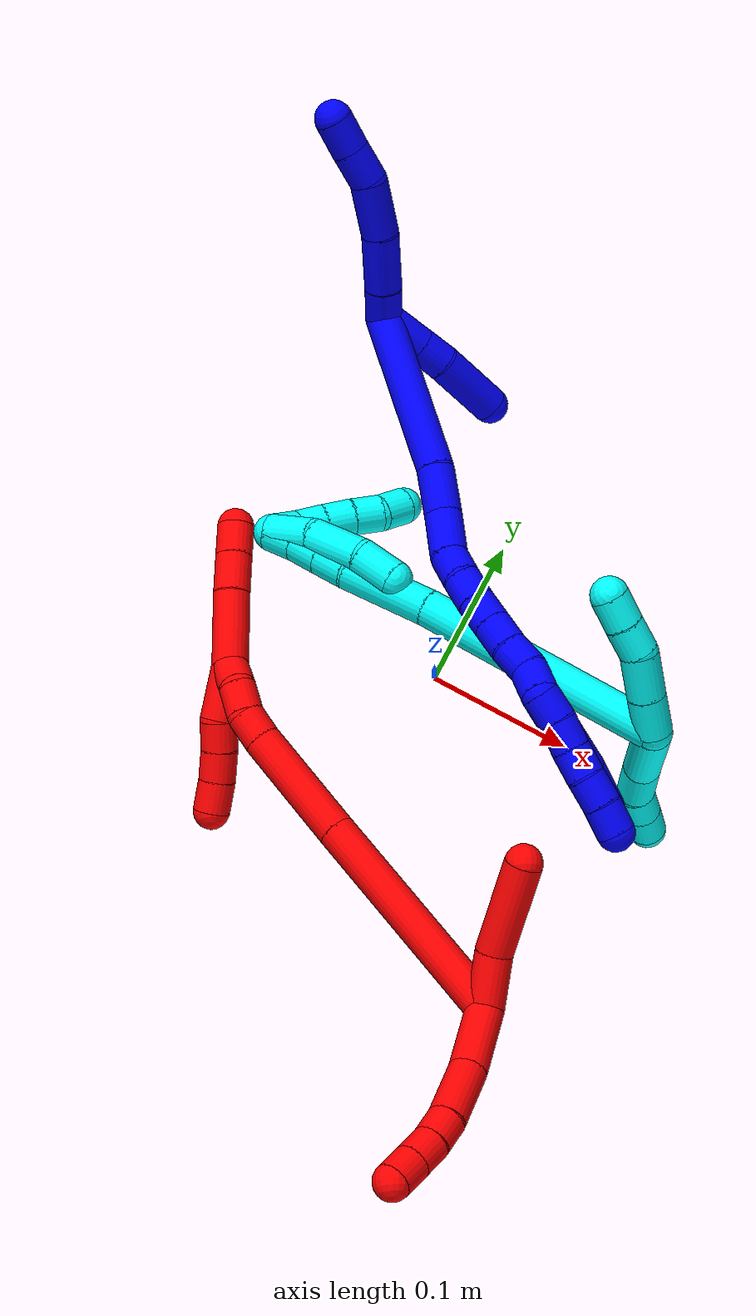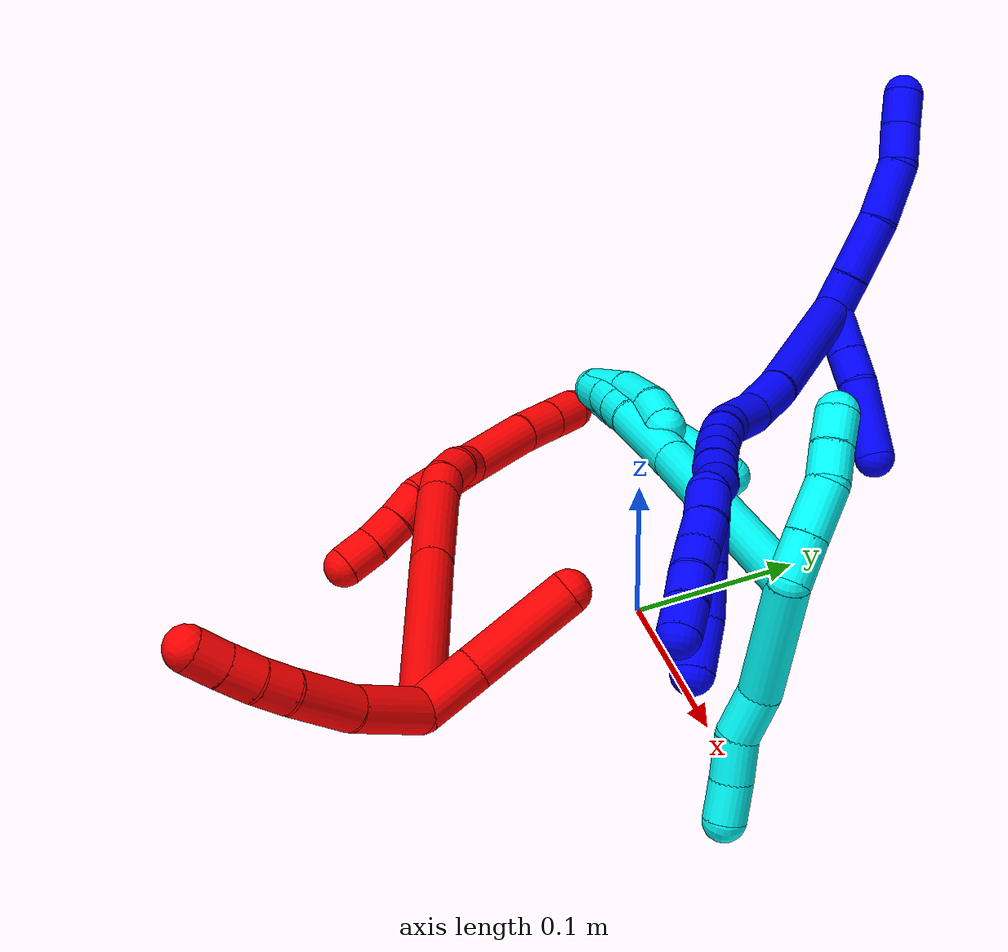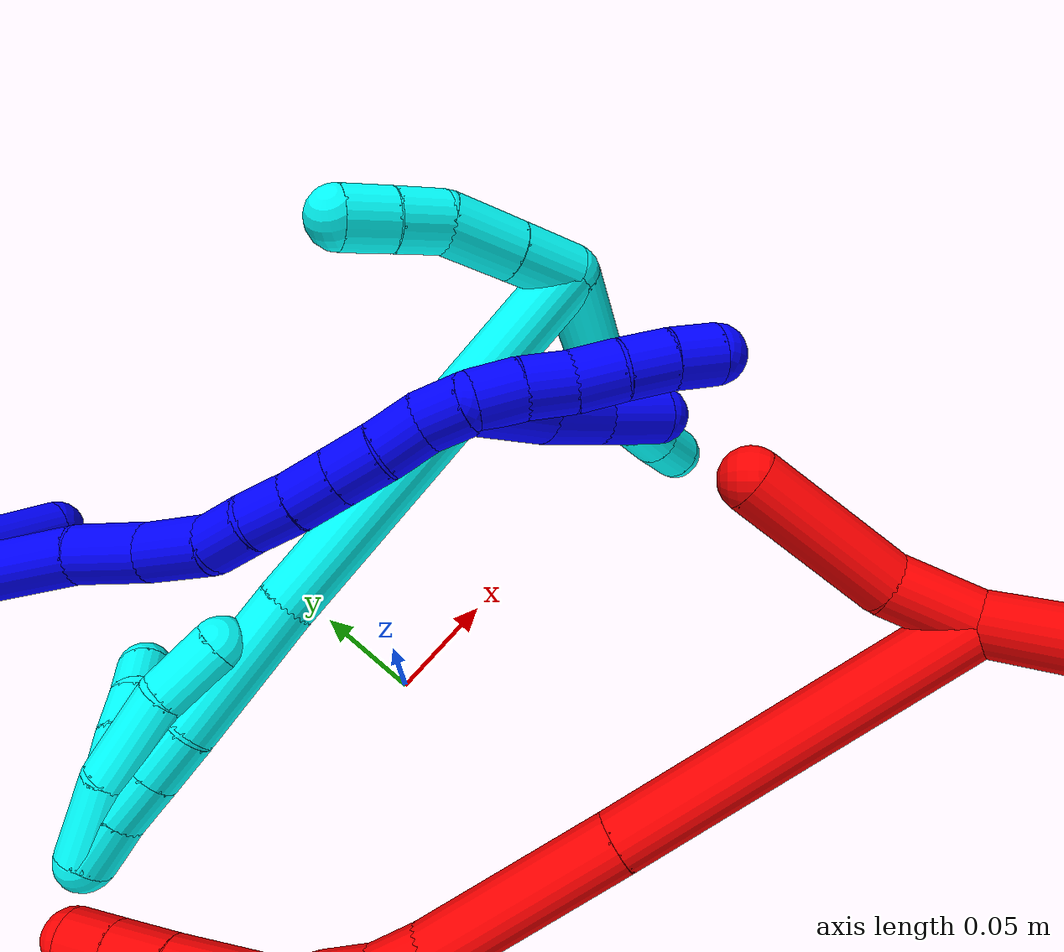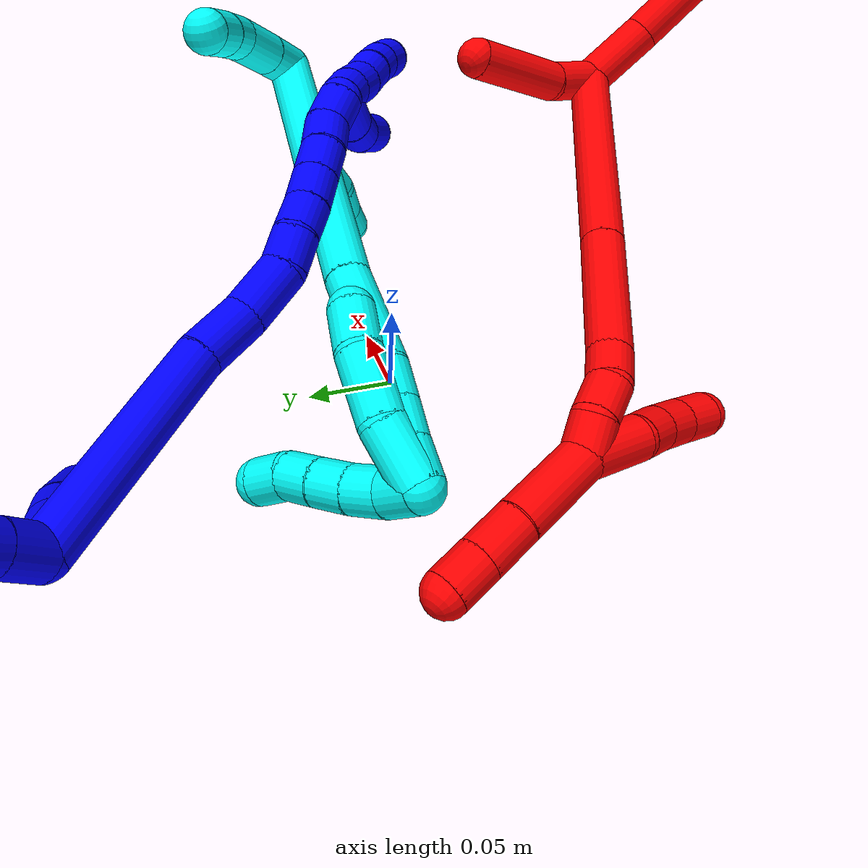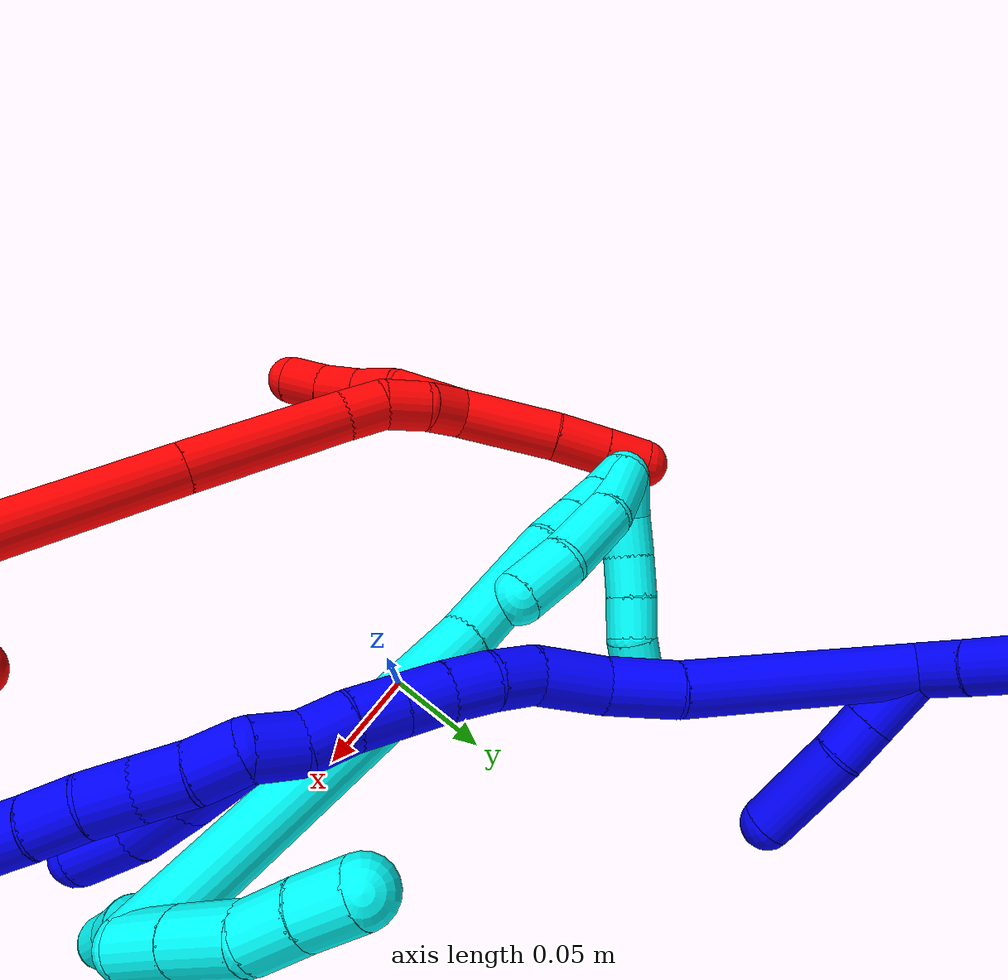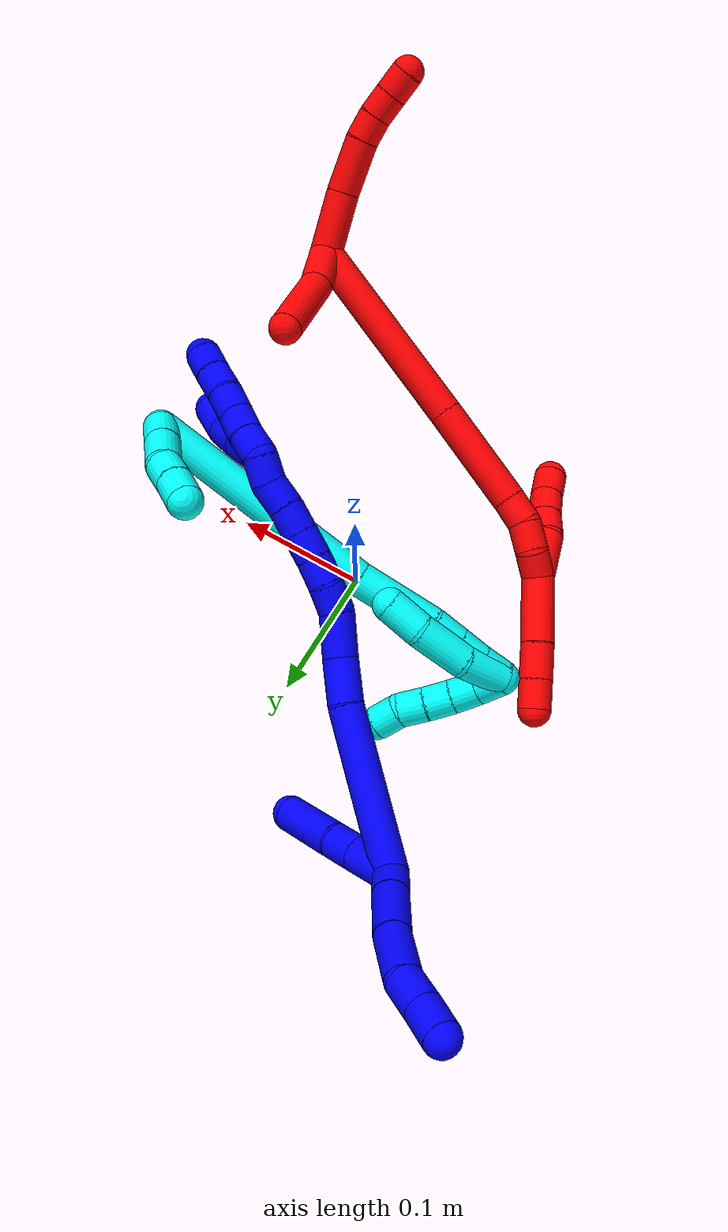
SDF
<sdf version="1.7">
 <world name="default">
  <plugin name="TubeGeneratorPlugin" filename="libtube_generator_plugin.so"/>
  <model name="photoneo_s_sensor">
   <static>1</static>
   <pose>0 0 2 1.57079 1.57079 3.14159</pose>
   <link name="link">
    <inertial><mass>0.1</mass></inertial>
    <sensor name="sensor" type="depth">
     <update_rate>30</update_rate>
     <camera>
      <horizontal_fov>1.22</horizontal_fov>
      <image><width>1920</width><height>1200</height><format>B8G8R8</format></image>
      <clip><near>0.1</near><far>4</far></clip>
      <depth_camera><output>points</output></depth_camera>
     </camera>
     <plugin name="camera_plugin" filename="libgazebo_ros_depth_camera.so">
      <baseline>0.2</baseline>
      <alwaysOn>1</alwaysOn>
      <updateRate>0.0</updateRate>
      <cameraName>camera_ir</cameraName>
      <imageTopicName>/camera/color/image_raw</imageTopicName>
      <cameraInfoTopicName>/camera/color/camera_info</cameraInfoTopicName>
      <depthImageTopicName>/camera/depth/image_raw</depthImageTopicName>
      <depthImageCameraInfoTopicName>/camera/depth/camera_info</depthImageCameraInfoTopicName>
      <pointCloudTopicName>/camera/depth/points</pointCloudTopicName>
      <frameName>fr_optical</frameName>
      <pointCloudCutoff>0.1</pointCloudCutoff>
      <pointCloudCutoffMax>2.0</pointCloudCutoffMax>
      <distortionK1>0</distortionK1>
      <distortionK2>0</distortionK2>
      <distortionK3>0</distortionK3>
      <distortionT1>0</distortionT1>
      <distortionT2>0</distortionT2>
      <CxPrime>0</CxPrime>
      <Cx>0</Cx>
      <Cy>0</Cy>
      <focalLength>0</focalLength>
      <hackBaseline>0</hackBaseline>
     </plugin>
    </sensor>
   </link>
  </model>
  <gravity>0 0 -9.8</gravity>
  <magnetic_field>6e-06 2.3e-05 -4.2e-05</magnetic_field>
  <atmosphere type="adiabatic"/>
  <physics name="default_physics" default="0" type="ode">
   <max_step_size>0.003</max_step_size>
   <real_time_factor>1</real_time_factor>
   <real_time_update_rate>1000</real_time_update_rate>
   <max_contacts>10000</max_contacts>
   <ode>
    <solver>
     <type>quick</type>
     <iters>100</iters>
     <sor>1.3</sor>
     <use_dynamic_moi_rescaling>0</use_dynamic_moi_rescaling>
    </solver>
    <constraints>
     <contact_max_correcting_vel>0</contact_max_correcting_vel>
     <contact_surface_layer>0.001</contact_surface_layer>
     <cfm>0</cfm>
     <erp>0.2</erp>
    </constraints>
   </ode>
  </physics>
  <scene><ambient>0.4 0.4 0.4 1</ambient><background>0.7 0.7 0.7 1</background><shadows>0</shadows></scene>
  <audio><device>default</device></audio>
  <spherical_coordinates>
   <surface_model>EARTH_WGS84</surface_model>
   <latitude_deg>0</latitude_deg>
   <longitude_deg>0</longitude_deg>
   <elevation>0</elevation>
   <heading_deg>0</heading_deg>
  </spherical_coordinates>
  <model name="bin">
   <static>1</static>
   <link name="bottom">
    <collision name="collision-bottom">
     <pose>0 0 -0.01 0 -0 0</pose>
     <geometry><box><size>0.8 0.6 0.02</size></box></geometry>
     <surface>
      <friction><ode><mu>100</mu><mu2>100</mu2></ode></friction>
      <contact><collide_bitmask>65535</collide_bitmask></contact>
     </surface>
    </collision>
   </link>
   <link name="west_wall">
    <collision name="collision-west_wall">
     <pose>-0.41 0 0.1 0 -0 0</pose>
     <geometry><box><size>0.02 0.6 0.2</size></box></geometry>
     <surface>
      <friction><ode><mu>100</mu><mu2>100</mu2></ode></friction>
      <contact><collide_bitmask>65535</collide_bitmask></contact>
     </surface>
    </collision>
   </link>
   <link name="east_wall">
    <collision name="collision-east_wall">
     <pose>0.41 0 0.1 0 -0 0</pose>
     <geometry><box><size>0.02 0.6 0.2</size></box></geometry>
     <surface>
      <friction><ode><mu>100</mu><mu2>100</mu2></ode></friction>
      <contact><collide_bitmask>65535</collide_bitmask></contact>
     </surface>
    </collision>
   </link>
   <link name="south_wall">
    <collision name="collision-south_wall">
     <pose>0 -0.31 0.1 0 -0 0</pose>
     <geometry><box><size>0.8 0.02 0.2</size></box></geometry>
     <surface>
      <friction><ode><mu>100</mu><mu2>100</mu2></ode></friction>
      <contact><collide_bitmask>65535</collide_bitmask></contact>
     </surface>
    </collision>
   </link>
   <link name="north_wall">
    <collision name="collision-north_wall">
     <pose>0 0.31 0.1 0 -0 0</pose>
     <geometry><box><size>0.8 0.02 0.2</size></box></geometry>
     <surface>
      <friction><ode><mu>100</mu><mu2>100</mu2></ode></friction>
      <contact><collide_bitmask>65535</collide_bitmask></contact>
     </surface>
    </collision>
   </link>
  </model>
  <model name="1">
   <static>0</static>
   <link name="1">
    <collision name="collision-cylinder-e_1_2_8">
     <pose>0.00226 0.003421 0.011406 -0.291426 0.187548 -0.027603</pose>
     <geometry><cylinder><radius>0.0125</radius><length>0.02424</length></cylinder></geometry>
     <surface>
      <friction><ode><mu>1.16</mu><mu2>1.16</mu2><slip1>0</slip1><slip2>0</slip2></ode></friction>
      <contact><ode><kp>1e+06</kp><kd>1</kd><max_vel>0</max_vel><min_depth>0.001</min_depth></ode></contact>
     </surface>
    </collision>
    <visual name="visual-cylinder-e_1_2_8">
     <pose>0.00226 0.003421 0.011406 -0.291426 0.187548 -0.027603</pose>
     <geometry><cylinder><radius>0.0125</radius><length>0.02424</length></cylinder></geometry>
     <material><ambient>0 0 1 1</ambient></material>
    </visual>
    <collision name="collision-cylinder-e_2_8_9">
     <pose>0.006936 0.01257 0.041662 -0.294959 0.12202 -0.018149</pose>
     <geometry><cylinder><radius>0.0125</radius><length>0.039698</length></cylinder></geometry>
     <surface>
      <friction><ode><mu>1.16</mu><mu2>1.16</mu2><slip1>0</slip1><slip2>0</slip2></ode></friction>
      <contact><ode><kp>1e+06</kp><kd>1</kd><max_vel>0</max_vel><min_depth>0.001</min_depth></ode></contact>
     </surface>
    </collision>
    <visual name="visual-cylinder-e_2_8_9">
     <pose>0.006936 0.01257 0.041662 -0.294959 0.12202 -0.018149</pose>
     <geometry><cylinder><radius>0.0125</radius><length>0.039698</length></cylinder></geometry>
     <material><ambient>0 0 1 1</ambient></material>
    </visual>
    <collision name="collision-cylinder-e_3_9_10">
     <pose>0.009455 0.022124 0.079303 -0.200947 0.005383 -0.000543</pose>
     <geometry><cylinder><radius>0.0125</radius><length>0.038353</length></cylinder></geometry>
     <surface>
      <friction><ode><mu>1.16</mu><mu2>1.16</mu2><slip1>0</slip1><slip2>0</slip2></ode></friction>
      <contact><ode><kp>1e+06</kp><kd>1</kd><max_vel>0</max_vel><min_depth>0.001</min_depth></ode></contact>
     </surface>
    </collision>
    <visual name="visual-cylinder-e_3_9_10">
     <pose>0.009455 0.022124 0.079303 -0.200947 0.005383 -0.000543</pose>
     <geometry><cylinder><radius>0.0125</radius><length>0.038353</length></cylinder></geometry>
     <material><ambient>0 0 1 1</ambient></material>
    </visual>
    <collision name="collision-cylinder-e_4_10_11">
     <pose>0.006926 0.025656 0.110028 0.024785 -0.216944 -0.002699</pose>
     <geometry><cylinder><radius>0.0125</radius><length>0.024451</length></cylinder></geometry>
     <surface>
      <friction><ode><mu>1.16</mu><mu2>1.16</mu2><slip1>0</slip1><slip2>0</slip2></ode></friction>
      <contact><ode><kp>1e+06</kp><kd>1</kd><max_vel>0</max_vel><min_depth>0.001</min_depth></ode></contact>
     </surface>
    </collision>
    <visual name="visual-cylinder-e_4_10_11">
     <pose>0.006926 0.025656 0.110028 0.024785 -0.216944 -0.002699</pose>
     <geometry><cylinder><radius>0.0125</radius><length>0.024451</length></cylinder></geometry>
     <material><ambient>0 0 1 1</ambient></material>
    </visual>
    <collision name="collision-cylinder-e_5_11_6">
     <pose>0.002055 0.025388 0.133375 -0.00246 -0.193798 0.000239</pose>
     <geometry><cylinder><radius>0.0125</radius><length>0.023257</length></cylinder></geometry>
     <surface>
      <friction><ode><mu>1.16</mu><mu2>1.16</mu2><slip1>0</slip1><slip2>0</slip2></ode></friction>
      <contact><ode><kp>1e+06</kp><kd>1</kd><max_vel>0</max_vel><min_depth>0.001</min_depth></ode></contact>
     </surface>
    </collision>
    <visual name="visual-cylinder-e_5_11_6">
     <pose>0.002055 0.025388 0.133375 -0.00246 -0.193798 0.000239</pose>
     <geometry><cylinder><radius>0.0125</radius><length>0.023257</length></cylinder></geometry>
     <material><ambient>0 0 1 1</ambient></material>
    </visual>
    <collision name="collision-cylinder-e_1_2_12">
     <pose>0.005718 0.005351 -0.013522 -2.76478 0.374634 -1.56485</pose>
     <geometry><cylinder><radius>0.0125</radius><length>0.031251</length></cylinder></geometry>
     <surface>
      <friction><ode><mu>1.16</mu><mu2>1.16</mu2><slip1>0</slip1><slip2>0</slip2></ode></friction>
      <contact><ode><kp>1e+06</kp><kd>1</kd><max_vel>0</max_vel><min_depth>0.001</min_depth></ode></contact>
     </surface>
    </collision>
    <visual name="visual-cylinder-e_1_2_12">
     <pose>0.005718 0.005351 -0.013522 -2.76478 0.374634 -1.56485</pose>
     <geometry><cylinder><radius>0.0125</radius><length>0.031251</length></cylinder></geometry>
     <material><ambient>0 0 1 1</ambient></material>
    </visual>
    <collision name="collision-cylinder-e_2_12_13">
     <pose>0.01517 0.014178 -0.03589 -2.76717 0.374271 -1.57039</pose>
     <geometry><cylinder><radius>0.0125</radius><length>0.020426</length></cylinder></geometry>
     <surface>
      <friction><ode><mu>1.16</mu><mu2>1.16</mu2><slip1>0</slip1><slip2>0</slip2></ode></friction>
      <contact><ode><kp>1e+06</kp><kd>1</kd><max_vel>0</max_vel><min_depth>0.001</min_depth></ode></contact>
     </surface>
    </collision>
    <visual name="visual-cylinder-e_2_12_13">
     <pose>0.01517 0.014178 -0.03589 -2.76717 0.374271 -1.57039</pose>
     <geometry><cylinder><radius>0.0125</radius><length>0.020426</length></cylinder></geometry>
     <material><ambient>0 0 1 1</ambient></material>
    </visual>
    <collision name="collision-cylinder-e_3_13_5">
     <pose>0.023992 0.025159 -0.067134 -2.81828 0.212205 -1.15707</pose>
     <geometry><cylinder><radius>0.0125</radius><length>0.048323</length></cylinder></geometry>
     <surface>
      <friction><ode><mu>1.16</mu><mu2>1.16</mu2><slip1>0</slip1><slip2>0</slip2></ode></friction>
      <contact><ode><kp>1e+06</kp><kd>1</kd><max_vel>0</max_vel><min_depth>0.001</min_depth></ode></contact>
     </surface>
    </collision>
    <visual name="visual-cylinder-e_3_13_5">
     <pose>0.023992 0.025159 -0.067134 -2.81828 0.212205 -1.15707</pose>
     <geometry><cylinder><radius>0.0125</radius><length>0.048323</length></cylinder></geometry>
     <material><ambient>0 0 1 1</ambient></material>
    </visual>
    <collision name="collision-cylinder-e_1_2_14">
     <pose>0.040869 -0.024186 -0.032321 2.49916 0.791557 1.79656</pose>
     <geometry><cylinder><radius>0.0125</radius><length>0.114889</length></cylinder></geometry>
     <surface>
      <friction><ode><mu>1.16</mu><mu2>1.16</mu2><slip1>0</slip1><slip2>0</slip2></ode></friction>
      <contact><ode><kp>1e+06</kp><kd>1</kd><max_vel>0</max_vel><min_depth>0.001</min_depth></ode></contact>
     </surface>
    </collision>
    <visual name="visual-cylinder-e_1_2_14">
     <pose>0.040869 -0.024186 -0.032321 2.49916 0.791557 1.79656</pose>
     <geometry><cylinder><radius>0.0125</radius><length>0.114889</length></cylinder></geometry>
     <material><ambient>0 0 1 1</ambient></material>
    </visual>
    <collision name="collision-cylinder-e_2_14_15">
     <pose>0.091678 -0.057185 -0.0741 2.39154 0.655509 1.42484</pose>
     <geometry><cylinder><radius>0.0125</radius><length>0.032615</length></cylinder></geometry>
     <surface>
      <friction><ode><mu>1.16</mu><mu2>1.16</mu2><slip1>0</slip1><slip2>0</slip2></ode></friction>
      <contact><ode><kp>1e+06</kp><kd>1</kd><max_vel>0</max_vel><min_depth>0.001</min_depth></ode></contact>
     </surface>
    </collision>
    <visual name="visual-cylinder-e_2_14_15">
     <pose>0.091678 -0.057185 -0.0741 2.39154 0.655509 1.42484</pose>
     <geometry><cylinder><radius>0.0125</radius><length>0.032615</length></cylinder></geometry>
     <material><ambient>0 0 1 1</ambient></material>
    </visual>
    <collision name="collision-cylinder-e_3_15_16">
     <pose>0.113107 -0.075386 -0.089575 2.14075 0.800314 1.31672</pose>
     <geometry><cylinder><radius>0.0125</radius><length>0.032021</length></cylinder></geometry>
     <surface>
      <friction><ode><mu>1.16</mu><mu2>1.16</mu2><slip1>0</slip1><slip2>0</slip2></ode></friction>
      <contact><ode><kp>1e+06</kp><kd>1</kd><max_vel>0</max_vel><min_depth>0.001</min_depth></ode></contact>
     </surface>
    </collision>
    <visual name="visual-cylinder-e_3_15_16">
     <pose>0.113107 -0.075386 -0.089575 2.14075 0.800314 1.31672</pose>
     <geometry><cylinder><radius>0.0125</radius><length>0.032021</length></cylinder></geometry>
     <material><ambient>0 0 1 1</ambient></material>
    </visual>
    <collision name="collision-cylinder-e_4_16_17">
     <pose>0.133764 -0.088071 -0.09868 2.32346 1.11307 1.9244</pose>
     <geometry><cylinder><radius>0.0125</radius><length>0.02044</length></cylinder></geometry>
     <surface>
      <friction><ode><mu>1.16</mu><mu2>1.16</mu2><slip1>0</slip1><slip2>0</slip2></ode></friction>
      <contact><ode><kp>1e+06</kp><kd>1</kd><max_vel>0</max_vel><min_depth>0.001</min_depth></ode></contact>
     </surface>
    </collision>
    <visual name="visual-cylinder-e_4_16_17">
     <pose>0.133764 -0.088071 -0.09868 2.32346 1.11307 1.9244</pose>
     <geometry><cylinder><radius>0.0125</radius><length>0.02044</length></cylinder></geometry>
     <material><ambient>0 0 1 1</ambient></material>
    </visual>
    <collision name="collision-cylinder-e_5_17_18">
     <pose>0.151429 -0.094012 -0.106328 2.61606 1.01543 2.24091</pose>
     <geometry><cylinder><radius>0.0125</radius><length>0.020001</length></cylinder></geometry>
     <surface>
      <friction><ode><mu>1.16</mu><mu2>1.16</mu2><slip1>0</slip1><slip2>0</slip2></ode></friction>
      <contact><ode><kp>1e+06</kp><kd>1</kd><max_vel>0</max_vel><min_depth>0.001</min_depth></ode></contact>
     </surface>
    </collision>
    <visual name="visual-cylinder-e_5_17_18">
     <pose>0.151429 -0.094012 -0.106328 2.61606 1.01543 2.24091</pose>
     <geometry><cylinder><radius>0.0125</radius><length>0.020001</length></cylinder></geometry>
     <material><ambient>0 0 1 1</ambient></material>
    </visual>
    <collision name="collision-cylinder-e_6_18_19">
     <pose>0.168746 -0.098687 -0.115154 2.69751 1.07914 2.42056</pose>
     <geometry><cylinder><radius>0.0125</radius><length>0.020008</length></cylinder></geometry>
     <surface>
      <friction><ode><mu>1.16</mu><mu2>1.16</mu2><slip1>0</slip1><slip2>0</slip2></ode></friction>
      <contact><ode><kp>1e+06</kp><kd>1</kd><max_vel>0</max_vel><min_depth>0.001</min_depth></ode></contact>
     </surface>
    </collision>
    <visual name="visual-cylinder-e_6_18_19">
     <pose>0.168746 -0.098687 -0.115154 2.69751 1.07914 2.42056</pose>
     <geometry><cylinder><radius>0.0125</radius><length>0.020008</length></cylinder></geometry>
     <material><ambient>0 0 1 1</ambient></material>
    </visual>
    <collision name="collision-cylinder-e_7_19_20">
     <pose>0.186379 -0.102726 -0.123698 2.70252 1.07844 2.42774</pose>
     <geometry><cylinder><radius>0.0125</radius><length>0.020005</length></cylinder></geometry>
     <surface>
      <friction><ode><mu>1.16</mu><mu2>1.16</mu2><slip1>0</slip1><slip2>0</slip2></ode></friction>
      <contact><ode><kp>1e+06</kp><kd>1</kd><max_vel>0</max_vel><min_depth>0.001</min_depth></ode></contact>
     </surface>
    </collision>
    <visual name="visual-cylinder-e_7_19_20">
     <pose>0.186379 -0.102726 -0.123698 2.70252 1.07844 2.42774</pose>
     <geometry><cylinder><radius>0.0125</radius><length>0.020005</length></cylinder></geometry>
     <material><ambient>0 0 1 1</ambient></material>
    </visual>
    <collision name="collision-cylinder-e_8_20_21">
     <pose>0.203984 -0.10552 -0.132698 2.97692 1.0724 2.86563</pose>
     <geometry><cylinder><radius>0.0125</radius><length>0.020016</length></cylinder></geometry>
     <surface>
      <friction><ode><mu>1.16</mu><mu2>1.16</mu2><slip1>0</slip1><slip2>0</slip2></ode></friction>
      <contact><ode><kp>1e+06</kp><kd>1</kd><max_vel>0</max_vel><min_depth>0.001</min_depth></ode></contact>
     </surface>
    </collision>
    <visual name="visual-cylinder-e_8_20_21">
     <pose>0.203984 -0.10552 -0.132698 2.97692 1.0724 2.86563</pose>
     <geometry><cylinder><radius>0.0125</radius><length>0.020016</length></cylinder></geometry>
     <material><ambient>0 0 1 1</ambient></material>
    </visual>
    <collision name="collision-cylinder-e_9_21_1">
     <pose>0.221201 -0.110136 -0.141208 2.35074 1.00165 1.83859</pose>
     <geometry><cylinder><radius>0.0125</radius><length>0.020005</length></cylinder></geometry>
     <surface>
      <friction><ode><mu>1.16</mu><mu2>1.16</mu2><slip1>0</slip1><slip2>0</slip2></ode></friction>
      <contact><ode><kp>1e+06</kp><kd>1</kd><max_vel>0</max_vel><min_depth>0.001</min_depth></ode></contact>
     </surface>
    </collision>
    <visual name="visual-cylinder-e_9_21_1">
     <pose>0.221201 -0.110136 -0.141208 2.35074 1.00165 1.83859</pose>
     <geometry><cylinder><radius>0.0125</radius><length>0.020005</length></cylinder></geometry>
     <material><ambient>0 0 1 1</ambient></material>
    </visual>
    <collision name="collision-cylinder-e_1_1_22">
     <pose>0.230147 -0.11219 -0.163843 -3.0475 0.027502 -0.568369</pose>
     <geometry><cylinder><radius>0.0125</radius><length>0.03787</length></cylinder></geometry>
     <surface>
      <friction><ode><mu>1.16</mu><mu2>1.16</mu2><slip1>0</slip1><slip2>0</slip2></ode></friction>
      <contact><ode><kp>1e+06</kp><kd>1</kd><max_vel>0</max_vel><min_depth>0.001</min_depth></ode></contact>
     </surface>
    </collision>
    <visual name="visual-cylinder-e_1_1_22">
     <pose>0.230147 -0.11219 -0.163843 -3.0475 0.027502 -0.568369</pose>
     <geometry><cylinder><radius>0.0125</radius><length>0.03787</length></cylinder></geometry>
     <material><ambient>0 0 1 1</ambient></material>
    </visual>
    <collision name="collision-cylinder-e_2_22_23">
     <pose>0.232952 -0.109369 -0.19838 -3.07525 0.14426 -2.28057</pose>
     <geometry><cylinder><radius>0.0125</radius><length>0.031785</length></cylinder></geometry>
     <surface>
      <friction><ode><mu>1.16</mu><mu2>1.16</mu2><slip1>0</slip1><slip2>0</slip2></ode></friction>
      <contact><ode><kp>1e+06</kp><kd>1</kd><max_vel>0</max_vel><min_depth>0.001</min_depth></ode></contact>
     </surface>
    </collision>
    <visual name="visual-cylinder-e_2_22_23">
     <pose>0.232952 -0.109369 -0.19838 -3.07525 0.14426 -2.28057</pose>
     <geometry><cylinder><radius>0.0125</radius><length>0.031785</length></cylinder></geometry>
     <material><ambient>0 0 1 1</ambient></material>
    </visual>
    <collision name="collision-cylinder-e_3_23_4">
     <pose>0.239813 -0.10983 -0.22846 3.03749 0.306373 2.49072</pose>
     <geometry><cylinder><radius>0.0125</radius><length>0.030345</length></cylinder></geometry>
     <surface>
      <friction><ode><mu>1.16</mu><mu2>1.16</mu2><slip1>0</slip1><slip2>0</slip2></ode></friction>
      <contact><ode><kp>1e+06</kp><kd>1</kd><max_vel>0</max_vel><min_depth>0.001</min_depth></ode></contact>
     </surface>
    </collision>
    <visual name="visual-cylinder-e_3_23_4">
     <pose>0.239813 -0.10983 -0.22846 3.03749 0.306373 2.49072</pose>
     <geometry><cylinder><radius>0.0125</radius><length>0.030345</length></cylinder></geometry>
     <material><ambient>0 0 1 1</ambient></material>
    </visual>
    <collision name="collision-cylinder-e_1_1_24">
     <pose>0.235595 -0.115019 -0.152953 3.01033 0.639595 2.74976</pose>
     <geometry><cylinder><radius>0.0125</radius><length>0.02</length></cylinder></geometry>
     <surface>
      <friction><ode><mu>1.16</mu><mu2>1.16</mu2><slip1>0</slip1><slip2>0</slip2></ode></friction>
      <contact><ode><kp>1e+06</kp><kd>1</kd><max_vel>0</max_vel><min_depth>0.001</min_depth></ode></contact>
     </surface>
    </collision>
    <visual name="visual-cylinder-e_1_1_24">
     <pose>0.235595 -0.115019 -0.152953 3.01033 0.639595 2.74976</pose>
     <geometry><cylinder><radius>0.0125</radius><length>0.02</length></cylinder></geometry>
     <material><ambient>0 0 1 1</ambient></material>
    </visual>
    <collision name="collision-cylinder-e_2_24_25">
     <pose>0.246781 -0.118225 -0.169161 2.88605 0.548887 2.28542</pose>
     <geometry><cylinder><radius>0.0125</radius><length>0.02</length></cylinder></geometry>
     <surface>
      <friction><ode><mu>1.16</mu><mu2>1.16</mu2><slip1>0</slip1><slip2>0</slip2></ode></friction>
      <contact><ode><kp>1e+06</kp><kd>1</kd><max_vel>0</max_vel><min_depth>0.001</min_depth></ode></contact>
     </surface>
    </collision>
    <visual name="visual-cylinder-e_2_24_25">
     <pose>0.246781 -0.118225 -0.169161 2.88605 0.548887 2.28542</pose>
     <geometry><cylinder><radius>0.0125</radius><length>0.02</length></cylinder></geometry>
     <material><ambient>0 0 1 1</ambient></material>
    </visual>
    <collision name="collision-cylinder-e_3_25_26">
     <pose>0.258456 -0.122528 -0.184743 2.85664 0.702026 2.39486</pose>
     <geometry><cylinder><radius>0.0125</radius><length>0.02</length></cylinder></geometry>
     <surface>
      <friction><ode><mu>1.16</mu><mu2>1.16</mu2><slip1>0</slip1><slip2>0</slip2></ode></friction>
      <contact><ode><kp>1e+06</kp><kd>1</kd><max_vel>0</max_vel><min_depth>0.001</min_depth></ode></contact>
     </surface>
    </collision>
    <visual name="visual-cylinder-e_3_25_26">
     <pose>0.258456 -0.122528 -0.184743 2.85664 0.702026 2.39486</pose>
     <geometry><cylinder><radius>0.0125</radius><length>0.02</length></cylinder></geometry>
     <material><ambient>0 0 1 1</ambient></material>
    </visual>
    <collision name="collision-cylinder-e_4_26_27">
     <pose>0.270535 -0.126088 -0.200219 2.96989 0.597004 2.59612</pose>
     <geometry><cylinder><radius>0.0125</radius><length>0.02</length></cylinder></geometry>
     <surface>
      <friction><ode><mu>1.16</mu><mu2>1.16</mu2><slip1>0</slip1><slip2>0</slip2></ode></friction>
      <contact><ode><kp>1e+06</kp><kd>1</kd><max_vel>0</max_vel><min_depth>0.001</min_depth></ode></contact>
     </surface>
    </collision>
    <visual name="visual-cylinder-e_4_26_27">
     <pose>0.270535 -0.126088 -0.200219 2.96989 0.597004 2.59612</pose>
     <geometry><cylinder><radius>0.0125</radius><length>0.02</length></cylinder></geometry>
     <material><ambient>0 0 1 1</ambient></material>
    </visual>
    <collision name="collision-cylinder-e_5_27_3">
     <pose>0.280984 -0.129288 -0.216941 2.93608 0.503675 2.37924</pose>
     <geometry><cylinder><radius>0.0125</radius><length>0.02</length></cylinder></geometry>
     <surface>
      <friction><ode><mu>1.16</mu><mu2>1.16</mu2><slip1>0</slip1><slip2>0</slip2></ode></friction>
      <contact><ode><kp>1e+06</kp><kd>1</kd><max_vel>0</max_vel><min_depth>0.001</min_depth></ode></contact>
     </surface>
    </collision>
    <visual name="visual-cylinder-e_5_27_3">
     <pose>0.280984 -0.129288 -0.216941 2.93608 0.503675 2.37924</pose>
     <geometry><cylinder><radius>0.0125</radius><length>0.02</length></cylinder></geometry>
     <material><ambient>0 0 1 1</ambient></material>
    </visual>
    <collision name="collision-sphere-3">
     <pose>0.28581 -0.131075 -0.225515 0 -0 0</pose>
     <geometry><sphere><radius>0.0125</radius></sphere></geometry>
     <surface>
      <friction><ode><mu>1.16</mu><mu2>1.16</mu2><slip1>0</slip1><slip2>0</slip2></ode></friction>
      <contact><ode><kp>1e+06</kp><kd>1</kd><max_vel>0</max_vel><min_depth>0.001</min_depth></ode></contact>
     </surface>
    </collision>
    <visual name="visual-sphere-3">
     <pose>0.28581 -0.131075 -0.225515 0 -0 0</pose>
     <geometry><sphere><radius>0.0125</radius></sphere></geometry>
     <material><ambient>0 0 1 1</ambient></material>
    </visual>
    <collision name="collision-sphere-27">
     <pose>0.276157 -0.127501 -0.208367 0 -0 0</pose>
     <geometry><sphere><radius>0.0125</radius></sphere></geometry>
     <surface>
      <friction><ode><mu>1.16</mu><mu2>1.16</mu2><slip1>0</slip1><slip2>0</slip2></ode></friction>
      <contact><ode><kp>1e+06</kp><kd>1</kd><max_vel>0</max_vel><min_depth>0.001</min_depth></ode></contact>
     </surface>
    </collision>
    <visual name="visual-sphere-27">
     <pose>0.276157 -0.127501 -0.208367 0 -0 0</pose>
     <geometry><sphere><radius>0.0125</radius></sphere></geometry>
     <material><ambient>0 0 1 1</ambient></material>
    </visual>
    <collision name="collision-sphere-26">
     <pose>0.264914 -0.124675 -0.19207 0 -0 0</pose>
     <geometry><sphere><radius>0.0125</radius></sphere></geometry>
     <surface>
      <friction><ode><mu>1.16</mu><mu2>1.16</mu2><slip1>0</slip1><slip2>0</slip2></ode></friction>
      <contact><ode><kp>1e+06</kp><kd>1</kd><max_vel>0</max_vel><min_depth>0.001</min_depth></ode></contact>
     </surface>
    </collision>
    <visual name="visual-sphere-26">
     <pose>0.264914 -0.124675 -0.19207 0 -0 0</pose>
     <geometry><sphere><radius>0.0125</radius></sphere></geometry>
     <material><ambient>0 0 1 1</ambient></material>
    </visual>
    <collision name="collision-sphere-25">
     <pose>0.251998 -0.120382 -0.177415 0 -0 0</pose>
     <geometry><sphere><radius>0.0125</radius></sphere></geometry>
     <surface>
      <friction><ode><mu>1.16</mu><mu2>1.16</mu2><slip1>0</slip1><slip2>0</slip2></ode></friction>
      <contact><ode><kp>1e+06</kp><kd>1</kd><max_vel>0</max_vel><min_depth>0.001</min_depth></ode></contact>
     </surface>
    </collision>
    <visual name="visual-sphere-25">
     <pose>0.251998 -0.120382 -0.177415 0 -0 0</pose>
     <geometry><sphere><radius>0.0125</radius></sphere></geometry>
     <material><ambient>0 0 1 1</ambient></material>
    </visual>
    <collision name="collision-sphere-24">
     <pose>0.241564 -0.116069 -0.160907 0 -0 0</pose>
     <geometry><sphere><radius>0.0125</radius></sphere></geometry>
     <surface>
      <friction><ode><mu>1.16</mu><mu2>1.16</mu2><slip1>0</slip1><slip2>0</slip2></ode></friction>
      <contact><ode><kp>1e+06</kp><kd>1</kd><max_vel>0</max_vel><min_depth>0.001</min_depth></ode></contact>
     </surface>
    </collision>
    <visual name="visual-sphere-24">
     <pose>0.241564 -0.116069 -0.160907 0 -0 0</pose>
     <geometry><sphere><radius>0.0125</radius></sphere></geometry>
     <material><ambient>0 0 1 1</ambient></material>
    </visual>
    <collision name="collision-sphere-4">
     <pose>0.244389 -0.111333 -0.242848 0 -0 0</pose>
     <geometry><sphere><radius>0.0125</radius></sphere></geometry>
     <surface>
      <friction><ode><mu>1.16</mu><mu2>1.16</mu2><slip1>0</slip1><slip2>0</slip2></ode></friction>
      <contact><ode><kp>1e+06</kp><kd>1</kd><max_vel>0</max_vel><min_depth>0.001</min_depth></ode></contact>
     </surface>
    </collision>
    <visual name="visual-sphere-4">
     <pose>0.244389 -0.111333 -0.242848 0 -0 0</pose>
     <geometry><sphere><radius>0.0125</radius></sphere></geometry>
     <material><ambient>0 0 1 1</ambient></material>
    </visual>
    <collision name="collision-sphere-23">
     <pose>0.235237 -0.108327 -0.214073 0 -0 0</pose>
     <geometry><sphere><radius>0.0125</radius></sphere></geometry>
     <surface>
      <friction><ode><mu>1.16</mu><mu2>1.16</mu2><slip1>0</slip1><slip2>0</slip2></ode></friction>
      <contact><ode><kp>1e+06</kp><kd>1</kd><max_vel>0</max_vel><min_depth>0.001</min_depth></ode></contact>
     </surface>
    </collision>
    <visual name="visual-sphere-23">
     <pose>0.235237 -0.108327 -0.214073 0 -0 0</pose>
     <geometry><sphere><radius>0.0125</radius></sphere></geometry>
     <material><ambient>0 0 1 1</ambient></material>
    </visual>
    <collision name="collision-sphere-22">
     <pose>0.230668 -0.110412 -0.182687 0 -0 0</pose>
     <geometry><sphere><radius>0.0125</radius></sphere></geometry>
     <surface>
      <friction><ode><mu>1.16</mu><mu2>1.16</mu2><slip1>0</slip1><slip2>0</slip2></ode></friction>
      <contact><ode><kp>1e+06</kp><kd>1</kd><max_vel>0</max_vel><min_depth>0.001</min_depth></ode></contact>
     </surface>
    </collision>
    <visual name="visual-sphere-22">
     <pose>0.230668 -0.110412 -0.182687 0 -0 0</pose>
     <geometry><sphere><radius>0.0125</radius></sphere></geometry>
     <material><ambient>0 0 1 1</ambient></material>
    </visual>
    <collision name="collision-sphere-1">
     <pose>0.229626 -0.113969 -0.144998 0 -0 0</pose>
     <geometry><sphere><radius>0.0125</radius></sphere></geometry>
     <surface>
      <friction><ode><mu>1.16</mu><mu2>1.16</mu2><slip1>0</slip1><slip2>0</slip2></ode></friction>
      <contact><ode><kp>1e+06</kp><kd>1</kd><max_vel>0</max_vel><min_depth>0.001</min_depth></ode></contact>
     </surface>
    </collision>
    <visual name="visual-sphere-1">
     <pose>0.229626 -0.113969 -0.144998 0 -0 0</pose>
     <geometry><sphere><radius>0.0125</radius></sphere></geometry>
     <material><ambient>0 0 1 1</ambient></material>
    </visual>
    <collision name="collision-sphere-21">
     <pose>0.212775 -0.106304 -0.137417 0 -0 0</pose>
     <geometry><sphere><radius>0.0125</radius></sphere></geometry>
     <surface>
      <friction><ode><mu>1.16</mu><mu2>1.16</mu2><slip1>0</slip1><slip2>0</slip2></ode></friction>
      <contact><ode><kp>1e+06</kp><kd>1</kd><max_vel>0</max_vel><min_depth>0.001</min_depth></ode></contact>
     </surface>
    </collision>
    <visual name="visual-sphere-21">
     <pose>0.212775 -0.106304 -0.137417 0 -0 0</pose>
     <geometry><sphere><radius>0.0125</radius></sphere></geometry>
     <material><ambient>0 0 1 1</ambient></material>
    </visual>
    <collision name="collision-sphere-6">
     <pose>-0.000184 0.025416 0.144786 0 -0 0</pose>
     <geometry><sphere><radius>0.0125</radius></sphere></geometry>
     <surface>
      <friction><ode><mu>1.16</mu><mu2>1.16</mu2><slip1>0</slip1><slip2>0</slip2></ode></friction>
      <contact><ode><kp>1e+06</kp><kd>1</kd><max_vel>0</max_vel><min_depth>0.001</min_depth></ode></contact>
     </surface>
    </collision>
    <visual name="visual-sphere-6">
     <pose>-0.000184 0.025416 0.144786 0 -0 0</pose>
     <geometry><sphere><radius>0.0125</radius></sphere></geometry>
     <material><ambient>0 0 1 1</ambient></material>
    </visual>
    <collision name="collision-sphere-11">
     <pose>0.004295 0.02536 0.121964 0 -0 0</pose>
     <geometry><sphere><radius>0.0125</radius></sphere></geometry>
     <surface>
      <friction><ode><mu>1.16</mu><mu2>1.16</mu2><slip1>0</slip1><slip2>0</slip2></ode></friction>
      <contact><ode><kp>1e+06</kp><kd>1</kd><max_vel>0</max_vel><min_depth>0.001</min_depth></ode></contact>
     </surface>
    </collision>
    <visual name="visual-sphere-11">
     <pose>0.004295 0.02536 0.121964 0 -0 0</pose>
     <geometry><sphere><radius>0.0125</radius></sphere></geometry>
     <material><ambient>0 0 1 1</ambient></material>
    </visual>
    <collision name="collision-sphere-10">
     <pose>0.009558 0.025952 0.098093 0 -0 0</pose>
     <geometry><sphere><radius>0.0125</radius></sphere></geometry>
     <surface>
      <friction><ode><mu>1.16</mu><mu2>1.16</mu2><slip1>0</slip1><slip2>0</slip2></ode></friction>
      <contact><ode><kp>1e+06</kp><kd>1</kd><max_vel>0</max_vel><min_depth>0.001</min_depth></ode></contact>
     </surface>
    </collision>
    <visual name="visual-sphere-10">
     <pose>0.009558 0.025952 0.098093 0 -0 0</pose>
     <geometry><sphere><radius>0.0125</radius></sphere></geometry>
     <material><ambient>0 0 1 1</ambient></material>
    </visual>
    <collision name="collision-sphere-9">
     <pose>0.009352 0.018297 0.060512 0 -0 0</pose>
     <geometry><sphere><radius>0.0125</radius></sphere></geometry>
     <surface>
      <friction><ode><mu>1.16</mu><mu2>1.16</mu2><slip1>0</slip1><slip2>0</slip2></ode></friction>
      <contact><ode><kp>1e+06</kp><kd>1</kd><max_vel>0</max_vel><min_depth>0.001</min_depth></ode></contact>
     </surface>
    </collision>
    <visual name="visual-sphere-9">
     <pose>0.009352 0.018297 0.060512 0 -0 0</pose>
     <geometry><sphere><radius>0.0125</radius></sphere></geometry>
     <material><ambient>0 0 1 1</ambient></material>
    </visual>
    <collision name="collision-sphere-2">
     <geometry><sphere><radius>0.0125</radius></sphere></geometry>
     <surface>
      <friction><ode><mu>1.16</mu><mu2>1.16</mu2><slip1>0</slip1><slip2>0</slip2></ode></friction>
      <contact><ode><kp>1e+06</kp><kd>1</kd><max_vel>0</max_vel><min_depth>0.001</min_depth></ode></contact>
     </surface>
    </collision>
    <visual name="visual-sphere-2">
     <geometry><sphere><radius>0.0125</radius></sphere></geometry>
     <material><ambient>0 0 1 1</ambient></material>
    </visual>
    <collision name="collision-sphere-19">
     <pose>0.177565 -0.100716 -0.119419 0 -0 0</pose>
     <geometry><sphere><radius>0.0125</radius></sphere></geometry>
     <surface>
      <friction><ode><mu>1.16</mu><mu2>1.16</mu2><slip1>0</slip1><slip2>0</slip2></ode></friction>
      <contact><ode><kp>1e+06</kp><kd>1</kd><max_vel>0</max_vel><min_depth>0.001</min_depth></ode></contact>
     </surface>
    </collision>
    <visual name="visual-sphere-19">
     <pose>0.177565 -0.100716 -0.119419 0 -0 0</pose>
     <geometry><sphere><radius>0.0125</radius></sphere></geometry>
     <material><ambient>0 0 1 1</ambient></material>
    </visual>
    <collision name="collision-sphere-8">
     <pose>0.00452 0.006843 0.022811 0 -0 0</pose>
     <geometry><sphere><radius>0.0125</radius></sphere></geometry>
     <surface>
      <friction><ode><mu>1.16</mu><mu2>1.16</mu2><slip1>0</slip1><slip2>0</slip2></ode></friction>
      <contact><ode><kp>1e+06</kp><kd>1</kd><max_vel>0</max_vel><min_depth>0.001</min_depth></ode></contact>
     </surface>
    </collision>
    <visual name="visual-sphere-8">
     <pose>0.00452 0.006843 0.022811 0 -0 0</pose>
     <geometry><sphere><radius>0.0125</radius></sphere></geometry>
     <material><ambient>0 0 1 1</ambient></material>
    </visual>
    <collision name="collision-sphere-12">
     <pose>0.011436 0.010702 -0.027043 0 -0 0</pose>
     <geometry><sphere><radius>0.0125</radius></sphere></geometry>
     <surface>
      <friction><ode><mu>1.16</mu><mu2>1.16</mu2><slip1>0</slip1><slip2>0</slip2></ode></friction>
      <contact><ode><kp>1e+06</kp><kd>1</kd><max_vel>0</max_vel><min_depth>0.001</min_depth></ode></contact>
     </surface>
    </collision>
    <visual name="visual-sphere-12">
     <pose>0.011436 0.010702 -0.027043 0 -0 0</pose>
     <geometry><sphere><radius>0.0125</radius></sphere></geometry>
     <material><ambient>0 0 1 1</ambient></material>
    </visual>
    <collision name="collision-sphere-13">
     <pose>0.018903 0.017655 -0.044738 0 -0 0</pose>
     <geometry><sphere><radius>0.0125</radius></sphere></geometry>
     <surface>
      <friction><ode><mu>1.16</mu><mu2>1.16</mu2><slip1>0</slip1><slip2>0</slip2></ode></friction>
      <contact><ode><kp>1e+06</kp><kd>1</kd><max_vel>0</max_vel><min_depth>0.001</min_depth></ode></contact>
     </surface>
    </collision>
    <visual name="visual-sphere-13">
     <pose>0.018903 0.017655 -0.044738 0 -0 0</pose>
     <geometry><sphere><radius>0.0125</radius></sphere></geometry>
     <material><ambient>0 0 1 1</ambient></material>
    </visual>
    <collision name="collision-sphere-5">
     <pose>0.029081 0.032663 -0.089529 0 -0 0</pose>
     <geometry><sphere><radius>0.0125</radius></sphere></geometry>
     <surface>
      <friction><ode><mu>1.16</mu><mu2>1.16</mu2><slip1>0</slip1><slip2>0</slip2></ode></friction>
      <contact><ode><kp>1e+06</kp><kd>1</kd><max_vel>0</max_vel><min_depth>0.001</min_depth></ode></contact>
     </surface>
    </collision>
    <visual name="visual-sphere-5">
     <pose>0.029081 0.032663 -0.089529 0 -0 0</pose>
     <geometry><sphere><radius>0.0125</radius></sphere></geometry>
     <material><ambient>0 0 1 1</ambient></material>
    </visual>
    <collision name="collision-sphere-14">
     <pose>0.081738 -0.048373 -0.064641 0 -0 0</pose>
     <geometry><sphere><radius>0.0125</radius></sphere></geometry>
     <surface>
      <friction><ode><mu>1.16</mu><mu2>1.16</mu2><slip1>0</slip1><slip2>0</slip2></ode></friction>
      <contact><ode><kp>1e+06</kp><kd>1</kd><max_vel>0</max_vel><min_depth>0.001</min_depth></ode></contact>
     </surface>
    </collision>
    <visual name="visual-sphere-14">
     <pose>0.081738 -0.048373 -0.064641 0 -0 0</pose>
     <geometry><sphere><radius>0.0125</radius></sphere></geometry>
     <material><ambient>0 0 1 1</ambient></material>
    </visual>
    <collision name="collision-sphere-15">
     <pose>0.101618 -0.065998 -0.083558 0 -0 0</pose>
     <geometry><sphere><radius>0.0125</radius></sphere></geometry>
     <surface>
      <friction><ode><mu>1.16</mu><mu2>1.16</mu2><slip1>0</slip1><slip2>0</slip2></ode></friction>
      <contact><ode><kp>1e+06</kp><kd>1</kd><max_vel>0</max_vel><min_depth>0.001</min_depth></ode></contact>
     </surface>
    </collision>
    <visual name="visual-sphere-15">
     <pose>0.101618 -0.065998 -0.083558 0 -0 0</pose>
     <geometry><sphere><radius>0.0125</radius></sphere></geometry>
     <material><ambient>0 0 1 1</ambient></material>
    </visual>
    <collision name="collision-sphere-16">
     <pose>0.124596 -0.084775 -0.095592 0 -0 0</pose>
     <geometry><sphere><radius>0.0125</radius></sphere></geometry>
     <surface>
      <friction><ode><mu>1.16</mu><mu2>1.16</mu2><slip1>0</slip1><slip2>0</slip2></ode></friction>
      <contact><ode><kp>1e+06</kp><kd>1</kd><max_vel>0</max_vel><min_depth>0.001</min_depth></ode></contact>
     </surface>
    </collision>
    <visual name="visual-sphere-16">
     <pose>0.124596 -0.084775 -0.095592 0 -0 0</pose>
     <geometry><sphere><radius>0.0125</radius></sphere></geometry>
     <material><ambient>0 0 1 1</ambient></material>
    </visual>
    <collision name="collision-sphere-17">
     <pose>0.142932 -0.091367 -0.101767 0 -0 0</pose>
     <geometry><sphere><radius>0.0125</radius></sphere></geometry>
     <surface>
      <friction><ode><mu>1.16</mu><mu2>1.16</mu2><slip1>0</slip1><slip2>0</slip2></ode></friction>
      <contact><ode><kp>1e+06</kp><kd>1</kd><max_vel>0</max_vel><min_depth>0.001</min_depth></ode></contact>
     </surface>
    </collision>
    <visual name="visual-sphere-17">
     <pose>0.142932 -0.091367 -0.101767 0 -0 0</pose>
     <geometry><sphere><radius>0.0125</radius></sphere></geometry>
     <material><ambient>0 0 1 1</ambient></material>
    </visual>
    <collision name="collision-sphere-18">
     <pose>0.159926 -0.096658 -0.110889 0 -0 0</pose>
     <geometry><sphere><radius>0.0125</radius></sphere></geometry>
     <surface>
      <friction><ode><mu>1.16</mu><mu2>1.16</mu2><slip1>0</slip1><slip2>0</slip2></ode></friction>
      <contact><ode><kp>1e+06</kp><kd>1</kd><max_vel>0</max_vel><min_depth>0.001</min_depth></ode></contact>
     </surface>
    </collision>
    <visual name="visual-sphere-18">
     <pose>0.159926 -0.096658 -0.110889 0 -0 0</pose>
     <geometry><sphere><radius>0.0125</radius></sphere></geometry>
     <material><ambient>0 0 1 1</ambient></material>
    </visual>
    <collision name="collision-sphere-20">
     <pose>0.195194 -0.104736 -0.127978 0 -0 0</pose>
     <geometry><sphere><radius>0.0125</radius></sphere></geometry>
     <surface>
      <friction><ode><mu>1.16</mu><mu2>1.16</mu2><slip1>0</slip1><slip2>0</slip2></ode></friction>
      <contact><ode><kp>1e+06</kp><kd>1</kd><max_vel>0</max_vel><min_depth>0.001</min_depth></ode></contact>
     </surface>
    </collision>
    <visual name="visual-sphere-20">
     <pose>0.195194 -0.104736 -0.127978 0 -0 0</pose>
     <geometry><sphere><radius>0.0125</radius></sphere></geometry>
     <material><ambient>0 0 1 1</ambient></material>
    </visual>
    <inertial>
     <pose>0.112647 -0.050724 -0.07328 0 -0 0</pose>
     <mass>0.75</mass>
     <inertia>
      <ixx>0.000105</ixx>
      <ixy>0</ixy>
      <ixz>0</ixz>
      <iyy>0.000188</iyy>
      <iyz>0</iyz>
      <izz>-8.4e-05</izz>
     </inertia>
    </inertial>
   </link>
   <pose>-0.141675 0.193101 0.059323 -0.355622 -0.781799 -0.11508</pose>
  </model>
  <model name="2">
   <static>0</static>
   <link name="2">
    <collision name="collision-cylinder-e_1_2_8">
     <pose>0.004451 0.009796 0.021256 -0.431851 0.187938 -0.041339</pose>
     <geometry><cylinder><radius>0.0125</radius><length>0.047648</length></cylinder></geometry>
     <surface>
      <friction><ode><mu>1.16</mu><mu2>1.16</mu2><slip1>0</slip1><slip2>0</slip2></ode></friction>
      <contact><ode><kp>1e+06</kp><kd>1</kd><max_vel>0</max_vel><min_depth>0.001</min_depth></ode></contact>
     </surface>
    </collision>
    <visual name="visual-cylinder-e_1_2_8">
     <pose>0.004451 0.009796 0.021256 -0.431851 0.187938 -0.041339</pose>
     <geometry><cylinder><radius>0.0125</radius><length>0.047648</length></cylinder></geometry>
     <material><ambient>1 0 0 1</ambient></material>
    </visual>
    <collision name="collision-cylinder-e_2_8_9">
     <pose>0.014962 0.030632 0.059323 -0.581054 0.292666 -0.088076</pose>
     <geometry><cylinder><radius>0.0125</radius><length>0.042011</length></cylinder></geometry>
     <surface>
      <friction><ode><mu>1.16</mu><mu2>1.16</mu2><slip1>0</slip1><slip2>0</slip2></ode></friction>
      <contact><ode><kp>1e+06</kp><kd>1</kd><max_vel>0</max_vel><min_depth>0.001</min_depth></ode></contact>
     </surface>
    </collision>
    <visual name="visual-cylinder-e_2_8_9">
     <pose>0.014962 0.030632 0.059323 -0.581054 0.292666 -0.088076</pose>
     <geometry><cylinder><radius>0.0125</radius><length>0.042011</length></cylinder></geometry>
     <material><ambient>1 0 0 1</ambient></material>
    </visual>
    <collision name="collision-cylinder-e_3_9_10">
     <pose>0.023215 0.048253 0.083519 -0.727992 0.218092 -0.08337</pose>
     <geometry><cylinder><radius>0.0125</radius><length>0.020263</length></cylinder></geometry>
     <surface>
      <friction><ode><mu>1.16</mu><mu2>1.16</mu2><slip1>0</slip1><slip2>0</slip2></ode></friction>
      <contact><ode><kp>1e+06</kp><kd>1</kd><max_vel>0</max_vel><min_depth>0.001</min_depth></ode></contact>
     </surface>
    </collision>
    <visual name="visual-cylinder-e_3_9_10">
     <pose>0.023215 0.048253 0.083519 -0.727992 0.218092 -0.08337</pose>
     <geometry><cylinder><radius>0.0125</radius><length>0.020263</length></cylinder></geometry>
     <material><ambient>1 0 0 1</ambient></material>
    </visual>
    <collision name="collision-cylinder-e_4_10_11">
     <pose>0.027251 0.062351 0.097275 -0.867625 0.18503 -0.085906</pose>
     <geometry><cylinder><radius>0.0125</radius><length>0.02005</length></cylinder></geometry>
     <surface>
      <friction><ode><mu>1.16</mu><mu2>1.16</mu2><slip1>0</slip1><slip2>0</slip2></ode></friction>
      <contact><ode><kp>1e+06</kp><kd>1</kd><max_vel>0</max_vel><min_depth>0.001</min_depth></ode></contact>
     </surface>
    </collision>
    <visual name="visual-cylinder-e_4_10_11">
     <pose>0.027251 0.062351 0.097275 -0.867625 0.18503 -0.085906</pose>
     <geometry><cylinder><radius>0.0125</radius><length>0.02005</length></cylinder></geometry>
     <material><ambient>1 0 0 1</ambient></material>
    </visual>
    <collision name="collision-cylinder-e_5_11_6">
     <pose>0.031268 0.077457 0.109808 -0.888867 0.218681 -0.104459</pose>
     <geometry><cylinder><radius>0.0125</radius><length>0.020028</length></cylinder></geometry>
     <surface>
      <friction><ode><mu>1.16</mu><mu2>1.16</mu2><slip1>0</slip1><slip2>0</slip2></ode></friction>
      <contact><ode><kp>1e+06</kp><kd>1</kd><max_vel>0</max_vel><min_depth>0.001</min_depth></ode></contact>
     </surface>
    </collision>
    <visual name="visual-cylinder-e_5_11_6">
     <pose>0.031268 0.077457 0.109808 -0.888867 0.218681 -0.104459</pose>
     <geometry><cylinder><radius>0.0125</radius><length>0.020028</length></cylinder></geometry>
     <material><ambient>1 0 0 1</ambient></material>
    </visual>
    <collision name="collision-cylinder-e_1_2_12">
     <pose>0.008736 -0.001209 -0.016018 3.06629 0.498101 2.84749</pose>
     <geometry><cylinder><radius>0.0125</radius><length>0.03657</length></cylinder></geometry>
     <surface>
      <friction><ode><mu>1.16</mu><mu2>1.16</mu2><slip1>0</slip1><slip2>0</slip2></ode></friction>
      <contact><ode><kp>1e+06</kp><kd>1</kd><max_vel>0</max_vel><min_depth>0.001</min_depth></ode></contact>
     </surface>
    </collision>
    <visual name="visual-cylinder-e_1_2_12">
     <pose>0.008736 -0.001209 -0.016018 3.06629 0.498101 2.84749</pose>
     <geometry><cylinder><radius>0.0125</radius><length>0.03657</length></cylinder></geometry>
     <material><ambient>1 0 0 1</ambient></material>
    </visual>
    <collision name="collision-cylinder-e_2_12_5">
     <pose>0.039264 -0.006105 -0.05478 2.98085 0.757551 2.74222</pose>
     <geometry><cylinder><radius>0.0125</radius><length>0.06343</length></cylinder></geometry>
     <surface>
      <friction><ode><mu>1.16</mu><mu2>1.16</mu2><slip1>0</slip1><slip2>0</slip2></ode></friction>
      <contact><ode><kp>1e+06</kp><kd>1</kd><max_vel>0</max_vel><min_depth>0.001</min_depth></ode></contact>
     </surface>
    </collision>
    <visual name="visual-cylinder-e_2_12_5">
     <pose>0.039264 -0.006105 -0.05478 2.98085 0.757551 2.74222</pose>
     <geometry><cylinder><radius>0.0125</radius><length>0.06343</length></cylinder></geometry>
     <material><ambient>1 0 0 1</ambient></material>
    </visual>
    <collision name="collision-cylinder-e_1_2_13">
     <pose>-0.020335 0.037858 -0.064446 -2.61046 -0.265634 0.913173</pose>
     <geometry><cylinder><radius>0.0125</radius><length>0.154919</length></cylinder></geometry>
     <surface>
      <friction><ode><mu>1.16</mu><mu2>1.16</mu2><slip1>0</slip1><slip2>0</slip2></ode></friction>
      <contact><ode><kp>1e+06</kp><kd>1</kd><max_vel>0</max_vel><min_depth>0.001</min_depth></ode></contact>
     </surface>
    </collision>
    <visual name="visual-cylinder-e_1_2_13">
     <pose>-0.020335 0.037858 -0.064446 -2.61046 -0.265634 0.913173</pose>
     <geometry><cylinder><radius>0.0125</radius><length>0.154919</length></cylinder></geometry>
     <material><ambient>1 0 0 1</ambient></material>
    </visual>
    <collision name="collision-cylinder-e_2_13_14">
     <pose>-0.051206 0.095306 -0.163108 -2.62163 -0.261144 0.917156</pose>
     <geometry><cylinder><radius>0.0125</radius><length>0.081622</length></cylinder></geometry>
     <surface>
      <friction><ode><mu>1.16</mu><mu2>1.16</mu2><slip1>0</slip1><slip2>0</slip2></ode></friction>
      <contact><ode><kp>1e+06</kp><kd>1</kd><max_vel>0</max_vel><min_depth>0.001</min_depth></ode></contact>
     </surface>
    </collision>
    <visual name="visual-cylinder-e_2_13_14">
     <pose>-0.051206 0.095306 -0.163108 -2.62163 -0.261144 0.917156</pose>
     <geometry><cylinder><radius>0.0125</radius><length>0.081622</length></cylinder></geometry>
     <material><ambient>1 0 0 1</ambient></material>
    </visual>
    <collision name="collision-cylinder-e_3_14_15">
     <pose>-0.063221 0.119757 -0.206449 -2.65199 -0.141974 0.554618</pose>
     <geometry><cylinder><radius>0.0125</radius><length>0.020888</length></cylinder></geometry>
     <surface>
      <friction><ode><mu>1.16</mu><mu2>1.16</mu2><slip1>0</slip1><slip2>0</slip2></ode></friction>
      <contact><ode><kp>1e+06</kp><kd>1</kd><max_vel>0</max_vel><min_depth>0.001</min_depth></ode></contact>
     </surface>
    </collision>
    <visual name="visual-cylinder-e_3_14_15">
     <pose>-0.063221 0.119757 -0.206449 -2.65199 -0.141974 0.554618</pose>
     <geometry><cylinder><radius>0.0125</radius><length>0.020888</length></cylinder></geometry>
     <material><ambient>1 0 0 1</ambient></material>
    </visual>
    <collision name="collision-cylinder-e_4_15_16">
     <pose>-0.066332 0.126269 -0.22618 -2.98728 -0.15098 1.54889</pose>
     <geometry><cylinder><radius>0.0125</radius><length>0.021716</length></cylinder></geometry>
     <surface>
      <friction><ode><mu>1.16</mu><mu2>1.16</mu2><slip1>0</slip1><slip2>0</slip2></ode></friction>
      <contact><ode><kp>1e+06</kp><kd>1</kd><max_vel>0</max_vel><min_depth>0.001</min_depth></ode></contact>
     </surface>
    </collision>
    <visual name="visual-cylinder-e_4_15_16">
     <pose>-0.066332 0.126269 -0.22618 -2.98728 -0.15098 1.54889</pose>
     <geometry><cylinder><radius>0.0125</radius><length>0.021716</length></cylinder></geometry>
     <material><ambient>1 0 0 1</ambient></material>
    </visual>
    <collision name="collision-cylinder-e_5_16_1">
     <pose>-0.072819 0.128352 -0.246006 -3.09462 -0.484228 2.9519</pose>
     <geometry><cylinder><radius>0.0125</radius><length>0.020855</length></cylinder></geometry>
     <surface>
      <friction><ode><mu>1.16</mu><mu2>1.16</mu2><slip1>0</slip1><slip2>0</slip2></ode></friction>
      <contact><ode><kp>1e+06</kp><kd>1</kd><max_vel>0</max_vel><min_depth>0.001</min_depth></ode></contact>
     </surface>
    </collision>
    <visual name="visual-cylinder-e_5_16_1">
     <pose>-0.072819 0.128352 -0.246006 -3.09462 -0.484228 2.9519</pose>
     <geometry><cylinder><radius>0.0125</radius><length>0.020855</length></cylinder></geometry>
     <material><ambient>1 0 0 1</ambient></material>
    </visual>
    <collision name="collision-cylinder-e_1_1_17">
     <pose>-0.085833 0.131496 -0.238682 -0.162397 -0.453005 0.037504</pose>
     <geometry><cylinder><radius>0.0125</radius><length>0.037286</length></cylinder></geometry>
     <surface>
      <friction><ode><mu>1.16</mu><mu2>1.16</mu2><slip1>0</slip1><slip2>0</slip2></ode></friction>
      <contact><ode><kp>1e+06</kp><kd>1</kd><max_vel>0</max_vel><min_depth>0.001</min_depth></ode></contact>
     </surface>
    </collision>
    <visual name="visual-cylinder-e_1_1_17">
     <pose>-0.085833 0.131496 -0.238682 -0.162397 -0.453005 0.037504</pose>
     <geometry><cylinder><radius>0.0125</radius><length>0.037286</length></cylinder></geometry>
     <material><ambient>1 0 0 1</ambient></material>
    </visual>
    <collision name="collision-cylinder-e_2_17_18">
     <pose>-0.099132 0.132853 -0.21353 0.155846 -0.532828 -0.042611</pose>
     <geometry><cylinder><radius>0.0125</radius><length>0.020235</length></cylinder></geometry>
     <surface>
      <friction><ode><mu>1.16</mu><mu2>1.16</mu2><slip1>0</slip1><slip2>0</slip2></ode></friction>
      <contact><ode><kp>1e+06</kp><kd>1</kd><max_vel>0</max_vel><min_depth>0.001</min_depth></ode></contact>
     </surface>
    </collision>
    <visual name="visual-cylinder-e_2_17_18">
     <pose>-0.099132 0.132853 -0.21353 0.155846 -0.532828 -0.042611</pose>
     <geometry><cylinder><radius>0.0125</radius><length>0.020235</length></cylinder></geometry>
     <material><ambient>1 0 0 1</ambient></material>
    </visual>
    <collision name="collision-cylinder-e_3_18_19">
     <pose>-0.109905 0.131208 -0.196054 0.03303 -0.565767 -0.009602</pose>
     <geometry><cylinder><radius>0.0125</radius><length>0.021018</length></cylinder></geometry>
     <surface>
      <friction><ode><mu>1.16</mu><mu2>1.16</mu2><slip1>0</slip1><slip2>0</slip2></ode></friction>
      <contact><ode><kp>1e+06</kp><kd>1</kd><max_vel>0</max_vel><min_depth>0.001</min_depth></ode></contact>
     </surface>
    </collision>
    <visual name="visual-cylinder-e_3_18_19">
     <pose>-0.109905 0.131208 -0.196054 0.03303 -0.565767 -0.009602</pose>
     <geometry><cylinder><radius>0.0125</radius><length>0.021018</length></cylinder></geometry>
     <material><ambient>1 0 0 1</ambient></material>
    </visual>
    <collision name="collision-cylinder-e_4_19_4">
     <pose>-0.121065 0.131811 -0.178033 -0.09765 -0.540992 0.027097</pose>
     <geometry><cylinder><radius>0.0125</radius><length>0.02146</length></cylinder></geometry>
     <surface>
      <friction><ode><mu>1.16</mu><mu2>1.16</mu2><slip1>0</slip1><slip2>0</slip2></ode></friction>
      <contact><ode><kp>1e+06</kp><kd>1</kd><max_vel>0</max_vel><min_depth>0.001</min_depth></ode></contact>
     </surface>
    </collision>
    <visual name="visual-cylinder-e_4_19_4">
     <pose>-0.121065 0.131811 -0.178033 -0.09765 -0.540992 0.027097</pose>
     <geometry><cylinder><radius>0.0125</radius><length>0.02146</length></cylinder></geometry>
     <material><ambient>1 0 0 1</ambient></material>
    </visual>
    <collision name="collision-cylinder-e_1_1_20">
     <pose>-0.07478 0.127458 -0.280551 3.08923 0.113611 2.27848</pose>
     <geometry><cylinder><radius>0.0125</radius><length>0.051052</length></cylinder></geometry>
     <surface>
      <friction><ode><mu>1.16</mu><mu2>1.16</mu2><slip1>0</slip1><slip2>0</slip2></ode></friction>
      <contact><ode><kp>1e+06</kp><kd>1</kd><max_vel>0</max_vel><min_depth>0.001</min_depth></ode></contact>
     </surface>
    </collision>
    <visual name="visual-cylinder-e_1_1_20">
     <pose>-0.07478 0.127458 -0.280551 3.08923 0.113611 2.27848</pose>
     <geometry><cylinder><radius>0.0125</radius><length>0.051052</length></cylinder></geometry>
     <material><ambient>1 0 0 1</ambient></material>
    </visual>
    <collision name="collision-cylinder-e_2_20_21">
     <pose>-0.071154 0.124712 -0.319197 3.03544 0.054588 0.949398</pose>
     <geometry><cylinder><radius>0.0125</radius><length>0.026829</length></cylinder></geometry>
     <surface>
      <friction><ode><mu>1.16</mu><mu2>1.16</mu2><slip1>0</slip1><slip2>0</slip2></ode></friction>
      <contact><ode><kp>1e+06</kp><kd>1</kd><max_vel>0</max_vel><min_depth>0.001</min_depth></ode></contact>
     </surface>
    </collision>
    <visual name="visual-cylinder-e_2_20_21">
     <pose>-0.071154 0.124712 -0.319197 3.03544 0.054588 0.949398</pose>
     <geometry><cylinder><radius>0.0125</radius><length>0.026829</length></cylinder></geometry>
     <material><ambient>1 0 0 1</ambient></material>
    </visual>
    <collision name="collision-cylinder-e_3_21_3">
     <pose>-0.069823 0.122063 -0.34349 3.03004 0.054158 0.903332</pose>
     <geometry><cylinder><radius>0.0125</radius><length>0.022119</length></cylinder></geometry>
     <surface>
      <friction><ode><mu>1.16</mu><mu2>1.16</mu2><slip1>0</slip1><slip2>0</slip2></ode></friction>
      <contact><ode><kp>1e+06</kp><kd>1</kd><max_vel>0</max_vel><min_depth>0.001</min_depth></ode></contact>
     </surface>
    </collision>
    <visual name="visual-cylinder-e_3_21_3">
     <pose>-0.069823 0.122063 -0.34349 3.03004 0.054158 0.903332</pose>
     <geometry><cylinder><radius>0.0125</radius><length>0.022119</length></cylinder></geometry>
     <material><ambient>1 0 0 1</ambient></material>
    </visual>
    <collision name="collision-sphere-3">
     <pose>-0.069225 0.120834 -0.354465 0 -0 0</pose>
     <geometry><sphere><radius>0.0125</radius></sphere></geometry>
     <surface>
      <friction><ode><mu>1.16</mu><mu2>1.16</mu2><slip1>0</slip1><slip2>0</slip2></ode></friction>
      <contact><ode><kp>1e+06</kp><kd>1</kd><max_vel>0</max_vel><min_depth>0.001</min_depth></ode></contact>
     </surface>
    </collision>
    <visual name="visual-sphere-3">
     <pose>-0.069225 0.120834 -0.354465 0 -0 0</pose>
     <geometry><sphere><radius>0.0125</radius></sphere></geometry>
     <material><ambient>1 0 0 1</ambient></material>
    </visual>
    <collision name="collision-sphere-21">
     <pose>-0.070422 0.123293 -0.332516 0 -0 0</pose>
     <geometry><sphere><radius>0.0125</radius></sphere></geometry>
     <surface>
      <friction><ode><mu>1.16</mu><mu2>1.16</mu2><slip1>0</slip1><slip2>0</slip2></ode></friction>
      <contact><ode><kp>1e+06</kp><kd>1</kd><max_vel>0</max_vel><min_depth>0.001</min_depth></ode></contact>
     </surface>
    </collision>
    <visual name="visual-sphere-21">
     <pose>-0.070422 0.123293 -0.332516 0 -0 0</pose>
     <geometry><sphere><radius>0.0125</radius></sphere></geometry>
     <material><ambient>1 0 0 1</ambient></material>
    </visual>
    <collision name="collision-sphere-20">
     <pose>-0.071886 0.126131 -0.305878 0 -0 0</pose>
     <geometry><sphere><radius>0.0125</radius></sphere></geometry>
     <surface>
      <friction><ode><mu>1.16</mu><mu2>1.16</mu2><slip1>0</slip1><slip2>0</slip2></ode></friction>
      <contact><ode><kp>1e+06</kp><kd>1</kd><max_vel>0</max_vel><min_depth>0.001</min_depth></ode></contact>
     </surface>
    </collision>
    <visual name="visual-sphere-20">
     <pose>-0.071886 0.126131 -0.305878 0 -0 0</pose>
     <geometry><sphere><radius>0.0125</radius></sphere></geometry>
     <material><ambient>1 0 0 1</ambient></material>
    </visual>
    <collision name="collision-sphere-4">
     <pose>-0.12659 0.132708 -0.168879 0 -0 0</pose>
     <geometry><sphere><radius>0.0125</radius></sphere></geometry>
     <surface>
      <friction><ode><mu>1.16</mu><mu2>1.16</mu2><slip1>0</slip1><slip2>0</slip2></ode></friction>
      <contact><ode><kp>1e+06</kp><kd>1</kd><max_vel>0</max_vel><min_depth>0.001</min_depth></ode></contact>
     </surface>
    </collision>
    <visual name="visual-sphere-4">
     <pose>-0.12659 0.132708 -0.168879 0 -0 0</pose>
     <geometry><sphere><radius>0.0125</radius></sphere></geometry>
     <material><ambient>1 0 0 1</ambient></material>
    </visual>
    <collision name="collision-sphere-6">
     <pose>0.033441 0.085046 0.11597 0 -0 0</pose>
     <geometry><sphere><radius>0.0125</radius></sphere></geometry>
     <surface>
      <friction><ode><mu>1.16</mu><mu2>1.16</mu2><slip1>0</slip1><slip2>0</slip2></ode></friction>
      <contact><ode><kp>1e+06</kp><kd>1</kd><max_vel>0</max_vel><min_depth>0.001</min_depth></ode></contact>
     </surface>
    </collision>
    <visual name="visual-sphere-6">
     <pose>0.033441 0.085046 0.11597 0 -0 0</pose>
     <geometry><sphere><radius>0.0125</radius></sphere></geometry>
     <material><ambient>1 0 0 1</ambient></material>
    </visual>
    <collision name="collision-sphere-11">
     <pose>0.029096 0.069868 0.103647 0 -0 0</pose>
     <geometry><sphere><radius>0.0125</radius></sphere></geometry>
     <surface>
      <friction><ode><mu>1.16</mu><mu2>1.16</mu2><slip1>0</slip1><slip2>0</slip2></ode></friction>
      <contact><ode><kp>1e+06</kp><kd>1</kd><max_vel>0</max_vel><min_depth>0.001</min_depth></ode></contact>
     </surface>
    </collision>
    <visual name="visual-sphere-11">
     <pose>0.029096 0.069868 0.103647 0 -0 0</pose>
     <geometry><sphere><radius>0.0125</radius></sphere></geometry>
     <material><ambient>1 0 0 1</ambient></material>
    </visual>
    <collision name="collision-sphere-10">
     <pose>0.025407 0.054834 0.090903 0 -0 0</pose>
     <geometry><sphere><radius>0.0125</radius></sphere></geometry>
     <surface>
      <friction><ode><mu>1.16</mu><mu2>1.16</mu2><slip1>0</slip1><slip2>0</slip2></ode></friction>
      <contact><ode><kp>1e+06</kp><kd>1</kd><max_vel>0</max_vel><min_depth>0.001</min_depth></ode></contact>
     </surface>
    </collision>
    <visual name="visual-sphere-10">
     <pose>0.025407 0.054834 0.090903 0 -0 0</pose>
     <geometry><sphere><radius>0.0125</radius></sphere></geometry>
     <material><ambient>1 0 0 1</ambient></material>
    </visual>
    <collision name="collision-sphere-9">
     <pose>0.021023 0.041672 0.076135 0 -0 0</pose>
     <geometry><sphere><radius>0.0125</radius></sphere></geometry>
     <surface>
      <friction><ode><mu>1.16</mu><mu2>1.16</mu2><slip1>0</slip1><slip2>0</slip2></ode></friction>
      <contact><ode><kp>1e+06</kp><kd>1</kd><max_vel>0</max_vel><min_depth>0.001</min_depth></ode></contact>
     </surface>
    </collision>
    <visual name="visual-sphere-9">
     <pose>0.021023 0.041672 0.076135 0 -0 0</pose>
     <geometry><sphere><radius>0.0125</radius></sphere></geometry>
     <material><ambient>1 0 0 1</ambient></material>
    </visual>
    <collision name="collision-sphere-2">
     <geometry><sphere><radius>0.0125</radius></sphere></geometry>
     <surface>
      <friction><ode><mu>1.16</mu><mu2>1.16</mu2><slip1>0</slip1><slip2>0</slip2></ode></friction>
      <contact><ode><kp>1e+06</kp><kd>1</kd><max_vel>0</max_vel><min_depth>0.001</min_depth></ode></contact>
     </surface>
    </collision>
    <visual name="visual-sphere-2">
     <geometry><sphere><radius>0.0125</radius></sphere></geometry>
     <material><ambient>1 0 0 1</ambient></material>
    </visual>
    <collision name="collision-sphere-19">
     <pose>-0.115539 0.130915 -0.187187 0 -0 0</pose>
     <geometry><sphere><radius>0.0125</radius></sphere></geometry>
     <surface>
      <friction><ode><mu>1.16</mu><mu2>1.16</mu2><slip1>0</slip1><slip2>0</slip2></ode></friction>
      <contact><ode><kp>1e+06</kp><kd>1</kd><max_vel>0</max_vel><min_depth>0.001</min_depth></ode></contact>
     </surface>
    </collision>
    <visual name="visual-sphere-19">
     <pose>-0.115539 0.130915 -0.187187 0 -0 0</pose>
     <geometry><sphere><radius>0.0125</radius></sphere></geometry>
     <material><ambient>1 0 0 1</ambient></material>
    </visual>
    <collision name="collision-sphere-8">
     <pose>0.008902 0.019592 0.042511 0 -0 0</pose>
     <geometry><sphere><radius>0.0125</radius></sphere></geometry>
     <surface>
      <friction><ode><mu>1.16</mu><mu2>1.16</mu2><slip1>0</slip1><slip2>0</slip2></ode></friction>
      <contact><ode><kp>1e+06</kp><kd>1</kd><max_vel>0</max_vel><min_depth>0.001</min_depth></ode></contact>
     </surface>
    </collision>
    <visual name="visual-sphere-8">
     <pose>0.008902 0.019592 0.042511 0 -0 0</pose>
     <geometry><sphere><radius>0.0125</radius></sphere></geometry>
     <material><ambient>1 0 0 1</ambient></material>
    </visual>
    <collision name="collision-sphere-12">
     <pose>0.017472 -0.002417 -0.032035 0 -0 0</pose>
     <geometry><sphere><radius>0.0125</radius></sphere></geometry>
     <surface>
      <friction><ode><mu>1.16</mu><mu2>1.16</mu2><slip1>0</slip1><slip2>0</slip2></ode></friction>
      <contact><ode><kp>1e+06</kp><kd>1</kd><max_vel>0</max_vel><min_depth>0.001</min_depth></ode></contact>
     </surface>
    </collision>
    <visual name="visual-sphere-12">
     <pose>0.017472 -0.002417 -0.032035 0 -0 0</pose>
     <geometry><sphere><radius>0.0125</radius></sphere></geometry>
     <material><ambient>1 0 0 1</ambient></material>
    </visual>
    <collision name="collision-sphere-5">
     <pose>0.061057 -0.009793 -0.077525 0 -0 0</pose>
     <geometry><sphere><radius>0.0125</radius></sphere></geometry>
     <surface>
      <friction><ode><mu>1.16</mu><mu2>1.16</mu2><slip1>0</slip1><slip2>0</slip2></ode></friction>
      <contact><ode><kp>1e+06</kp><kd>1</kd><max_vel>0</max_vel><min_depth>0.001</min_depth></ode></contact>
     </surface>
    </collision>
    <visual name="visual-sphere-5">
     <pose>0.061057 -0.009793 -0.077525 0 -0 0</pose>
     <geometry><sphere><radius>0.0125</radius></sphere></geometry>
     <material><ambient>1 0 0 1</ambient></material>
    </visual>
    <collision name="collision-sphere-13">
     <pose>-0.04067 0.075716 -0.128891 0 -0 0</pose>
     <geometry><sphere><radius>0.0125</radius></sphere></geometry>
     <surface>
      <friction><ode><mu>1.16</mu><mu2>1.16</mu2><slip1>0</slip1><slip2>0</slip2></ode></friction>
      <contact><ode><kp>1e+06</kp><kd>1</kd><max_vel>0</max_vel><min_depth>0.001</min_depth></ode></contact>
     </surface>
    </collision>
    <visual name="visual-sphere-13">
     <pose>-0.04067 0.075716 -0.128891 0 -0 0</pose>
     <geometry><sphere><radius>0.0125</radius></sphere></geometry>
     <material><ambient>1 0 0 1</ambient></material>
    </visual>
    <collision name="collision-sphere-14">
     <pose>-0.061743 0.114895 -0.197325 0 -0 0</pose>
     <geometry><sphere><radius>0.0125</radius></sphere></geometry>
     <surface>
      <friction><ode><mu>1.16</mu><mu2>1.16</mu2><slip1>0</slip1><slip2>0</slip2></ode></friction>
      <contact><ode><kp>1e+06</kp><kd>1</kd><max_vel>0</max_vel><min_depth>0.001</min_depth></ode></contact>
     </surface>
    </collision>
    <visual name="visual-sphere-14">
     <pose>-0.061743 0.114895 -0.197325 0 -0 0</pose>
     <geometry><sphere><radius>0.0125</radius></sphere></geometry>
     <material><ambient>1 0 0 1</ambient></material>
    </visual>
    <collision name="collision-sphere-15">
     <pose>-0.064699 0.124619 -0.215573 0 -0 0</pose>
     <geometry><sphere><radius>0.0125</radius></sphere></geometry>
     <surface>
      <friction><ode><mu>1.16</mu><mu2>1.16</mu2><slip1>0</slip1><slip2>0</slip2></ode></friction>
      <contact><ode><kp>1e+06</kp><kd>1</kd><max_vel>0</max_vel><min_depth>0.001</min_depth></ode></contact>
     </surface>
    </collision>
    <visual name="visual-sphere-15">
     <pose>-0.064699 0.124619 -0.215573 0 -0 0</pose>
     <geometry><sphere><radius>0.0125</radius></sphere></geometry>
     <material><ambient>1 0 0 1</ambient></material>
    </visual>
    <collision name="collision-sphere-16">
     <pose>-0.067965 0.127919 -0.236787 0 -0 0</pose>
     <geometry><sphere><radius>0.0125</radius></sphere></geometry>
     <surface>
      <friction><ode><mu>1.16</mu><mu2>1.16</mu2><slip1>0</slip1><slip2>0</slip2></ode></friction>
      <contact><ode><kp>1e+06</kp><kd>1</kd><max_vel>0</max_vel><min_depth>0.001</min_depth></ode></contact>
     </surface>
    </collision>
    <visual name="visual-sphere-16">
     <pose>-0.067965 0.127919 -0.236787 0 -0 0</pose>
     <geometry><sphere><radius>0.0125</radius></sphere></geometry>
     <material><ambient>1 0 0 1</ambient></material>
    </visual>
    <collision name="collision-sphere-1">
     <pose>-0.077673 0.128786 -0.255224 0 -0 0</pose>
     <geometry><sphere><radius>0.0125</radius></sphere></geometry>
     <surface>
      <friction><ode><mu>1.16</mu><mu2>1.16</mu2><slip1>0</slip1><slip2>0</slip2></ode></friction>
      <contact><ode><kp>1e+06</kp><kd>1</kd><max_vel>0</max_vel><min_depth>0.001</min_depth></ode></contact>
     </surface>
    </collision>
    <visual name="visual-sphere-1">
     <pose>-0.077673 0.128786 -0.255224 0 -0 0</pose>
     <geometry><sphere><radius>0.0125</radius></sphere></geometry>
     <material><ambient>1 0 0 1</ambient></material>
    </visual>
    <collision name="collision-sphere-18">
     <pose>-0.104271 0.131501 -0.204921 0 -0 0</pose>
     <geometry><sphere><radius>0.0125</radius></sphere></geometry>
     <surface>
      <friction><ode><mu>1.16</mu><mu2>1.16</mu2><slip1>0</slip1><slip2>0</slip2></ode></friction>
      <contact><ode><kp>1e+06</kp><kd>1</kd><max_vel>0</max_vel><min_depth>0.001</min_depth></ode></contact>
     </surface>
    </collision>
    <visual name="visual-sphere-18">
     <pose>-0.104271 0.131501 -0.204921 0 -0 0</pose>
     <geometry><sphere><radius>0.0125</radius></sphere></geometry>
     <material><ambient>1 0 0 1</ambient></material>
    </visual>
    <collision name="collision-sphere-17">
     <pose>-0.093992 0.134206 -0.22214 0 -0 0</pose>
     <geometry><sphere><radius>0.0125</radius></sphere></geometry>
     <surface>
      <friction><ode><mu>1.16</mu><mu2>1.16</mu2><slip1>0</slip1><slip2>0</slip2></ode></friction>
      <contact><ode><kp>1e+06</kp><kd>1</kd><max_vel>0</max_vel><min_depth>0.001</min_depth></ode></contact>
     </surface>
    </collision>
    <visual name="visual-sphere-17">
     <pose>-0.093992 0.134206 -0.22214 0 -0 0</pose>
     <geometry><sphere><radius>0.0125</radius></sphere></geometry>
     <material><ambient>1 0 0 1</ambient></material>
    </visual>
    <inertial>
     <pose>-0.031602 0.069862 -0.112014 0 -0 0</pose>
     <mass>0.75</mass>
     <inertia>
      <ixx>0.00052</ixx>
      <ixy>0</ixy>
      <ixz>0</ixz>
      <iyy>0.000227</iyy>
      <iyz>0</iyz>
      <izz>-0.000129</izz>
     </inertia>
    </inertial>
   </link>
   <pose>0.132111 -0.180097 0.121844 0.947157 -1.11255 1.15241</pose>
  </model>
  <model name="3">
   <static>0</static>
   <link name="3">
    <collision name="collision-cylinder-e_1_2_8">
     <pose>0.002747 -0.001176 -0.036383 3.10928 0.075308 2.33128</pose>
     <geometry><cylinder><radius>0.0125</radius><length>0.073011</length></cylinder></geometry>
     <surface>
      <friction><ode><mu>1.16</mu><mu2>1.16</mu2><slip1>0</slip1><slip2>0</slip2></ode></friction>
      <contact><ode><kp>1e+06</kp><kd>1</kd><max_vel>0</max_vel><min_depth>0.001</min_depth></ode></contact>
     </surface>
    </collision>
    <visual name="visual-cylinder-e_1_2_8">
     <pose>0.002747 -0.001176 -0.036383 3.10928 0.075308 2.33128</pose>
     <geometry><cylinder><radius>0.0125</radius><length>0.073011</length></cylinder></geometry>
     <material><ambient>0.003922 1 0.996078 1</ambient></material>
    </visual>
    <collision name="collision-cylinder-e_2_8_9">
     <pose>0.008447 -0.006964 -0.085827 2.80211 0.210129 1.10316</pose>
     <geometry><cylinder><radius>0.0125</radius><length>0.028326</length></cylinder></geometry>
     <surface>
      <friction><ode><mu>1.16</mu><mu2>1.16</mu2><slip1>0</slip1><slip2>0</slip2></ode></friction>
      <contact><ode><kp>1e+06</kp><kd>1</kd><max_vel>0</max_vel><min_depth>0.001</min_depth></ode></contact>
     </surface>
    </collision>
    <visual name="visual-cylinder-e_2_8_9">
     <pose>0.008447 -0.006964 -0.085827 2.80211 0.210129 1.10316</pose>
     <geometry><cylinder><radius>0.0125</radius><length>0.028326</length></cylinder></geometry>
     <material><ambient>0.003922 1 0.996078 1</ambient></material>
    </visual>
    <collision name="collision-cylinder-e_3_9_10">
     <pose>0.01655 -0.012227 -0.110549 3.08594 0.415162 2.8788</pose>
     <geometry><cylinder><radius>0.0125</radius><length>0.025527</length></cylinder></geometry>
     <surface>
      <friction><ode><mu>1.16</mu><mu2>1.16</mu2><slip1>0</slip1><slip2>0</slip2></ode></friction>
      <contact><ode><kp>1e+06</kp><kd>1</kd><max_vel>0</max_vel><min_depth>0.001</min_depth></ode></contact>
     </surface>
    </collision>
    <visual name="visual-cylinder-e_3_9_10">
     <pose>0.01655 -0.012227 -0.110549 3.08594 0.415162 2.8788</pose>
     <geometry><cylinder><radius>0.0125</radius><length>0.025527</length></cylinder></geometry>
     <material><ambient>0.003922 1 0.996078 1</ambient></material>
    </visual>
    <collision name="collision-cylinder-e_4_10_6">
     <pose>0.026881 -0.014178 -0.13247 3.01535 0.464642 2.61949</pose>
     <geometry><cylinder><radius>0.0125</radius><length>0.023136</length></cylinder></geometry>
     <surface>
      <friction><ode><mu>1.16</mu><mu2>1.16</mu2><slip1>0</slip1><slip2>0</slip2></ode></friction>
      <contact><ode><kp>1e+06</kp><kd>1</kd><max_vel>0</max_vel><min_depth>0.001</min_depth></ode></contact>
     </surface>
    </collision>
    <visual name="visual-cylinder-e_4_10_6">
     <pose>0.026881 -0.014178 -0.13247 3.01535 0.464642 2.61949</pose>
     <geometry><cylinder><radius>0.0125</radius><length>0.023136</length></cylinder></geometry>
     <material><ambient>0.003922 1 0.996078 1</ambient></material>
    </visual>
    <collision name="collision-cylinder-e_1_2_11">
     <pose>-0.008486 0.005383 0.009202 -0.52931 -0.672306 0.188828</pose>
     <geometry><cylinder><radius>0.0125</radius><length>0.027252</length></cylinder></geometry>
     <surface>
      <friction><ode><mu>1.16</mu><mu2>1.16</mu2><slip1>0</slip1><slip2>0</slip2></ode></friction>
      <contact><ode><kp>1e+06</kp><kd>1</kd><max_vel>0</max_vel><min_depth>0.001</min_depth></ode></contact>
     </surface>
    </collision>
    <visual name="visual-cylinder-e_1_2_11">
     <pose>-0.008486 0.005383 0.009202 -0.52931 -0.672306 0.188828</pose>
     <geometry><cylinder><radius>0.0125</radius><length>0.027252</length></cylinder></geometry>
     <material><ambient>0.003922 1 0.996078 1</ambient></material>
    </visual>
    <collision name="collision-cylinder-e_2_11_12">
     <pose>-0.026585 0.017219 0.028632 -0.562821 -0.671624 0.201117</pose>
     <geometry><cylinder><radius>0.0125</radius><length>0.030898</length></cylinder></geometry>
     <surface>
      <friction><ode><mu>1.16</mu><mu2>1.16</mu2><slip1>0</slip1><slip2>0</slip2></ode></friction>
      <contact><ode><kp>1e+06</kp><kd>1</kd><max_vel>0</max_vel><min_depth>0.001</min_depth></ode></contact>
     </surface>
    </collision>
    <visual name="visual-cylinder-e_2_11_12">
     <pose>-0.026585 0.017219 0.028632 -0.562821 -0.671624 0.201117</pose>
     <geometry><cylinder><radius>0.0125</radius><length>0.030898</length></cylinder></geometry>
     <material><ambient>0.003922 1 0.996078 1</ambient></material>
    </visual>
    <collision name="collision-cylinder-e_3_12_13">
     <pose>-0.045037 0.026188 0.044052 -0.451252 -0.992441 0.247274</pose>
     <geometry><cylinder><radius>0.0125</radius><length>0.021109</length></cylinder></geometry>
     <surface>
      <friction><ode><mu>1.16</mu><mu2>1.16</mu2><slip1>0</slip1><slip2>0</slip2></ode></friction>
      <contact><ode><kp>1e+06</kp><kd>1</kd><max_vel>0</max_vel><min_depth>0.001</min_depth></ode></contact>
     </surface>
    </collision>
    <visual name="visual-cylinder-e_3_12_13">
     <pose>-0.045037 0.026188 0.044052 -0.451252 -0.992441 0.247274</pose>
     <geometry><cylinder><radius>0.0125</radius><length>0.021109</length></cylinder></geometry>
     <material><ambient>0.003922 1 0.996078 1</ambient></material>
    </visual>
    <collision name="collision-cylinder-e_4_13_5">
     <pose>-0.0626 0.031689 0.053988 -0.561671 -0.999821 0.312536</pose>
     <geometry><cylinder><radius>0.0125</radius><length>0.020741</length></cylinder></geometry>
     <surface>
      <friction><ode><mu>1.16</mu><mu2>1.16</mu2><slip1>0</slip1><slip2>0</slip2></ode></friction>
      <contact><ode><kp>1e+06</kp><kd>1</kd><max_vel>0</max_vel><min_depth>0.001</min_depth></ode></contact>
     </surface>
    </collision>
    <visual name="visual-cylinder-e_4_13_5">
     <pose>-0.0626 0.031689 0.053988 -0.561671 -0.999821 0.312536</pose>
     <geometry><cylinder><radius>0.0125</radius><length>0.020741</length></cylinder></geometry>
     <material><ambient>0.003922 1 0.996078 1</ambient></material>
    </visual>
    <collision name="collision-cylinder-e_1_2_14">
     <pose>-0.083548 -0.006927 -0.024927 2.87054 -1.2705 -2.77577</pose>
     <geometry><cylinder><radius>0.0125</radius><length>0.174923</length></cylinder></geometry>
     <surface>
      <friction><ode><mu>1.16</mu><mu2>1.16</mu2><slip1>0</slip1><slip2>0</slip2></ode></friction>
      <contact><ode><kp>1e+06</kp><kd>1</kd><max_vel>0</max_vel><min_depth>0.001</min_depth></ode></contact>
     </surface>
    </collision>
    <visual name="visual-cylinder-e_1_2_14">
     <pose>-0.083548 -0.006927 -0.024927 2.87054 -1.2705 -2.77577</pose>
     <geometry><cylinder><radius>0.0125</radius><length>0.174923</length></cylinder></geometry>
     <material><ambient>0.003922 1 0.996078 1</ambient></material>
    </visual>
    <collision name="collision-cylinder-e_2_14_15">
     <pose>-0.196288 -0.018903 -0.05695 2.5232 -1.28085 -2.33166</pose>
     <geometry><cylinder><radius>0.0125</radius><length>0.060929</length></cylinder></geometry>
     <surface>
      <friction><ode><mu>1.16</mu><mu2>1.16</mu2><slip1>0</slip1><slip2>0</slip2></ode></friction>
      <contact><ode><kp>1e+06</kp><kd>1</kd><max_vel>0</max_vel><min_depth>0.001</min_depth></ode></contact>
     </surface>
    </collision>
    <visual name="visual-cylinder-e_2_14_15">
     <pose>-0.196288 -0.018903 -0.05695 2.5232 -1.28085 -2.33166</pose>
     <geometry><cylinder><radius>0.0125</radius><length>0.060929</length></cylinder></geometry>
     <material><ambient>0.003922 1 0.996078 1</ambient></material>
    </visual>
    <collision name="collision-cylinder-e_3_15_16">
     <pose>-0.235737 -0.024722 -0.067722 2.93518 -1.21986 -2.84731</pose>
     <geometry><cylinder><radius>0.0125</radius><length>0.021844</length></cylinder></geometry>
     <surface>
      <friction><ode><mu>1.16</mu><mu2>1.16</mu2><slip1>0</slip1><slip2>0</slip2></ode></friction>
      <contact><ode><kp>1e+06</kp><kd>1</kd><max_vel>0</max_vel><min_depth>0.001</min_depth></ode></contact>
     </surface>
    </collision>
    <visual name="visual-cylinder-e_3_15_16">
     <pose>-0.235737 -0.024722 -0.067722 2.93518 -1.21986 -2.84731</pose>
     <geometry><cylinder><radius>0.0125</radius><length>0.021844</length></cylinder></geometry>
     <material><ambient>0.003922 1 0.996078 1</ambient></material>
    </visual>
    <collision name="collision-cylinder-e_4_16_17">
     <pose>-0.25577 -0.026171 -0.074812 2.94527 -1.22867 -2.86418</pose>
     <geometry><cylinder><radius>0.0125</radius><length>0.020755</length></cylinder></geometry>
     <surface>
      <friction><ode><mu>1.16</mu><mu2>1.16</mu2><slip1>0</slip1><slip2>0</slip2></ode></friction>
      <contact><ode><kp>1e+06</kp><kd>1</kd><max_vel>0</max_vel><min_depth>0.001</min_depth></ode></contact>
     </surface>
    </collision>
    <visual name="visual-cylinder-e_4_16_17">
     <pose>-0.25577 -0.026171 -0.074812 2.94527 -1.22867 -2.86418</pose>
     <geometry><cylinder><radius>0.0125</radius><length>0.020755</length></cylinder></geometry>
     <material><ambient>0.003922 1 0.996078 1</ambient></material>
    </visual>
    <collision name="collision-cylinder-e_5_17_1">
     <pose>-0.275349 -0.028272 -0.082465 2.81793 -1.14287 -2.64429</pose>
     <geometry><cylinder><radius>0.0125</radius><length>0.021549</length></cylinder></geometry>
     <surface>
      <friction><ode><mu>1.16</mu><mu2>1.16</mu2><slip1>0</slip1><slip2>0</slip2></ode></friction>
      <contact><ode><kp>1e+06</kp><kd>1</kd><max_vel>0</max_vel><min_depth>0.001</min_depth></ode></contact>
     </surface>
    </collision>
    <visual name="visual-cylinder-e_5_17_1">
     <pose>-0.275349 -0.028272 -0.082465 2.81793 -1.14287 -2.64429</pose>
     <geometry><cylinder><radius>0.0125</radius><length>0.021549</length></cylinder></geometry>
     <material><ambient>0.003922 1 0.996078 1</ambient></material>
    </visual>
    <collision name="collision-cylinder-e_1_1_18">
     <pose>-0.280443 -0.02221 -0.091375 -2.12877 0.490278 -0.847426</pose>
     <geometry><cylinder><radius>0.0125</radius><length>0.02</length></cylinder></geometry>
     <surface>
      <friction><ode><mu>1.16</mu><mu2>1.16</mu2><slip1>0</slip1><slip2>0</slip2></ode></friction>
      <contact><ode><kp>1e+06</kp><kd>1</kd><max_vel>0</max_vel><min_depth>0.001</min_depth></ode></contact>
     </surface>
    </collision>
    <visual name="visual-cylinder-e_1_1_18">
     <pose>-0.280443 -0.02221 -0.091375 -2.12877 0.490278 -0.847426</pose>
     <geometry><cylinder><radius>0.0125</radius><length>0.02</length></cylinder></geometry>
     <material><ambient>0.003922 1 0.996078 1</ambient></material>
    </visual>
    <collision name="collision-cylinder-e_2_18_19">
     <pose>-0.270552 -0.006495 -0.098372 -1.84621 0.544724 -0.707298</pose>
     <geometry><cylinder><radius>0.0125</radius><length>0.02</length></cylinder></geometry>
     <surface>
      <friction><ode><mu>1.16</mu><mu2>1.16</mu2><slip1>0</slip1><slip2>0</slip2></ode></friction>
      <contact><ode><kp>1e+06</kp><kd>1</kd><max_vel>0</max_vel><min_depth>0.001</min_depth></ode></contact>
     </surface>
    </collision>
    <visual name="visual-cylinder-e_2_18_19">
     <pose>-0.270552 -0.006495 -0.098372 -1.84621 0.544724 -0.707298</pose>
     <geometry><cylinder><radius>0.0125</radius><length>0.02</length></cylinder></geometry>
     <material><ambient>0.003922 1 0.996078 1</ambient></material>
    </visual>
    <collision name="collision-cylinder-e_3_19_20">
     <pose>-0.259644 0.009804 -0.102147 -1.74849 0.60979 -0.719754</pose>
     <geometry><cylinder><radius>0.0125</radius><length>0.02</length></cylinder></geometry>
     <surface>
      <friction><ode><mu>1.16</mu><mu2>1.16</mu2><slip1>0</slip1><slip2>0</slip2></ode></friction>
      <contact><ode><kp>1e+06</kp><kd>1</kd><max_vel>0</max_vel><min_depth>0.001</min_depth></ode></contact>
     </surface>
    </collision>
    <visual name="visual-cylinder-e_3_19_20">
     <pose>-0.259644 0.009804 -0.102147 -1.74849 0.60979 -0.719754</pose>
     <geometry><cylinder><radius>0.0125</radius><length>0.02</length></cylinder></geometry>
     <material><ambient>0.003922 1 0.996078 1</ambient></material>
    </visual>
    <collision name="collision-cylinder-e_4_20_21">
     <pose>-0.247803 0.025574 -0.105416 -1.80282 0.657791 -0.814435</pose>
     <geometry><cylinder><radius>0.0125</radius><length>0.02</length></cylinder></geometry>
     <surface>
      <friction><ode><mu>1.16</mu><mu2>1.16</mu2><slip1>0</slip1><slip2>0</slip2></ode></friction>
      <contact><ode><kp>1e+06</kp><kd>1</kd><max_vel>0</max_vel><min_depth>0.001</min_depth></ode></contact>
     </surface>
    </collision>
    <visual name="visual-cylinder-e_4_20_21">
     <pose>-0.247803 0.025574 -0.105416 -1.80282 0.657791 -0.814435</pose>
     <geometry><cylinder><radius>0.0125</radius><length>0.02</length></cylinder></geometry>
     <material><ambient>0.003922 1 0.996078 1</ambient></material>
    </visual>
    <collision name="collision-cylinder-e_5_21_4">
     <pose>-0.237901 0.041574 -0.111331 -2.02923 0.38855 -0.613072</pose>
     <geometry><cylinder><radius>0.0125</radius><length>0.02</length></cylinder></geometry>
     <surface>
      <friction><ode><mu>1.16</mu><mu2>1.16</mu2><slip1>0</slip1><slip2>0</slip2></ode></friction>
      <contact><ode><kp>1e+06</kp><kd>1</kd><max_vel>0</max_vel><min_depth>0.001</min_depth></ode></contact>
     </surface>
    </collision>
    <visual name="visual-cylinder-e_5_21_4">
     <pose>-0.237901 0.041574 -0.111331 -2.02923 0.38855 -0.613072</pose>
     <geometry><cylinder><radius>0.0125</radius><length>0.02</length></cylinder></geometry>
     <material><ambient>0.003922 1 0.996078 1</ambient></material>
    </visual>
    <collision name="collision-cylinder-e_1_1_22">
     <pose>-0.271883 -0.024218 -0.077855 -0.554123 0.905727 -0.275003</pose>
     <geometry><cylinder><radius>0.0125</radius><length>0.033726</length></cylinder></geometry>
     <surface>
      <friction><ode><mu>1.16</mu><mu2>1.16</mu2><slip1>0</slip1><slip2>0</slip2></ode></friction>
      <contact><ode><kp>1e+06</kp><kd>1</kd><max_vel>0</max_vel><min_depth>0.001</min_depth></ode></contact>
     </surface>
    </collision>
    <visual name="visual-cylinder-e_1_1_22">
     <pose>-0.271883 -0.024218 -0.077855 -0.554123 0.905727 -0.275003</pose>
     <geometry><cylinder><radius>0.0125</radius><length>0.033726</length></cylinder></geometry>
     <material><ambient>0.003922 1 0.996078 1</ambient></material>
    </visual>
    <collision name="collision-cylinder-e_2_22_23">
     <pose>-0.241076 -0.016204 -0.061358 -0.320486 1.1401 -0.206483</pose>
     <geometry><cylinder><radius>0.0125</radius><length>0.038602</length></cylinder></geometry>
     <surface>
      <friction><ode><mu>1.16</mu><mu2>1.16</mu2><slip1>0</slip1><slip2>0</slip2></ode></friction>
      <contact><ode><kp>1e+06</kp><kd>1</kd><max_vel>0</max_vel><min_depth>0.001</min_depth></ode></contact>
     </surface>
    </collision>
    <visual name="visual-cylinder-e_2_22_23">
     <pose>-0.241076 -0.016204 -0.061358 -0.320486 1.1401 -0.206483</pose>
     <geometry><cylinder><radius>0.0125</radius><length>0.038602</length></cylinder></geometry>
     <material><ambient>0.003922 1 0.996078 1</ambient></material>
    </visual>
    <collision name="collision-cylinder-e_3_23_3">
     <pose>-0.20997 -0.013437 -0.051008 -0.084184 1.37351 -0.069036</pose>
     <geometry><cylinder><radius>0.0125</radius><length>0.027673</length></cylinder></geometry>
     <surface>
      <friction><ode><mu>1.16</mu><mu2>1.16</mu2><slip1>0</slip1><slip2>0</slip2></ode></friction>
      <contact><ode><kp>1e+06</kp><kd>1</kd><max_vel>0</max_vel><min_depth>0.001</min_depth></ode></contact>
     </surface>
    </collision>
    <visual name="visual-cylinder-e_3_23_3">
     <pose>-0.20997 -0.013437 -0.051008 -0.084184 1.37351 -0.069036</pose>
     <geometry><cylinder><radius>0.0125</radius><length>0.027673</length></cylinder></geometry>
     <material><ambient>0.003922 1 0.996078 1</ambient></material>
    </visual>
    <collision name="collision-sphere-3">
     <pose>-0.196402 -0.013209 -0.048306 0 -0 0</pose>
     <geometry><sphere><radius>0.0125</radius></sphere></geometry>
     <surface>
      <friction><ode><mu>1.16</mu><mu2>1.16</mu2><slip1>0</slip1><slip2>0</slip2></ode></friction>
      <contact><ode><kp>1e+06</kp><kd>1</kd><max_vel>0</max_vel><min_depth>0.001</min_depth></ode></contact>
     </surface>
    </collision>
    <visual name="visual-sphere-3">
     <pose>-0.196402 -0.013209 -0.048306 0 -0 0</pose>
     <geometry><sphere><radius>0.0125</radius></sphere></geometry>
     <material><ambient>0.003922 1 0.996078 1</ambient></material>
    </visual>
    <collision name="collision-sphere-23">
     <pose>-0.223538 -0.013665 -0.05371 0 -0 0</pose>
     <geometry><sphere><radius>0.0125</radius></sphere></geometry>
     <surface>
      <friction><ode><mu>1.16</mu><mu2>1.16</mu2><slip1>0</slip1><slip2>0</slip2></ode></friction>
      <contact><ode><kp>1e+06</kp><kd>1</kd><max_vel>0</max_vel><min_depth>0.001</min_depth></ode></contact>
     </surface>
    </collision>
    <visual name="visual-sphere-23">
     <pose>-0.223538 -0.013665 -0.05371 0 -0 0</pose>
     <geometry><sphere><radius>0.0125</radius></sphere></geometry>
     <material><ambient>0.003922 1 0.996078 1</ambient></material>
    </visual>
    <collision name="collision-sphere-22">
     <pose>-0.258614 -0.018742 -0.069006 0 -0 0</pose>
     <geometry><sphere><radius>0.0125</radius></sphere></geometry>
     <surface>
      <friction><ode><mu>1.16</mu><mu2>1.16</mu2><slip1>0</slip1><slip2>0</slip2></ode></friction>
      <contact><ode><kp>1e+06</kp><kd>1</kd><max_vel>0</max_vel><min_depth>0.001</min_depth></ode></contact>
     </surface>
    </collision>
    <visual name="visual-sphere-22">
     <pose>-0.258614 -0.018742 -0.069006 0 -0 0</pose>
     <geometry><sphere><radius>0.0125</radius></sphere></geometry>
     <material><ambient>0.003922 1 0.996078 1</ambient></material>
    </visual>
    <collision name="collision-sphere-4">
     <pose>-0.234112 0.049873 -0.115427 0 -0 0</pose>
     <geometry><sphere><radius>0.0125</radius></sphere></geometry>
     <surface>
      <friction><ode><mu>1.16</mu><mu2>1.16</mu2><slip1>0</slip1><slip2>0</slip2></ode></friction>
      <contact><ode><kp>1e+06</kp><kd>1</kd><max_vel>0</max_vel><min_depth>0.001</min_depth></ode></contact>
     </surface>
    </collision>
    <visual name="visual-sphere-4">
     <pose>-0.234112 0.049873 -0.115427 0 -0 0</pose>
     <geometry><sphere><radius>0.0125</radius></sphere></geometry>
     <material><ambient>0.003922 1 0.996078 1</ambient></material>
    </visual>
    <collision name="collision-sphere-21">
     <pose>-0.241689 0.033275 -0.107235 0 -0 0</pose>
     <geometry><sphere><radius>0.0125</radius></sphere></geometry>
     <surface>
      <friction><ode><mu>1.16</mu><mu2>1.16</mu2><slip1>0</slip1><slip2>0</slip2></ode></friction>
      <contact><ode><kp>1e+06</kp><kd>1</kd><max_vel>0</max_vel><min_depth>0.001</min_depth></ode></contact>
     </surface>
    </collision>
    <visual name="visual-sphere-21">
     <pose>-0.241689 0.033275 -0.107235 0 -0 0</pose>
     <geometry><sphere><radius>0.0125</radius></sphere></geometry>
     <material><ambient>0.003922 1 0.996078 1</ambient></material>
    </visual>
    <collision name="collision-sphere-20">
     <pose>-0.253917 0.017872 -0.103596 0 -0 0</pose>
     <geometry><sphere><radius>0.0125</radius></sphere></geometry>
     <surface>
      <friction><ode><mu>1.16</mu><mu2>1.16</mu2><slip1>0</slip1><slip2>0</slip2></ode></friction>
      <contact><ode><kp>1e+06</kp><kd>1</kd><max_vel>0</max_vel><min_depth>0.001</min_depth></ode></contact>
     </surface>
    </collision>
    <visual name="visual-sphere-20">
     <pose>-0.253917 0.017872 -0.103596 0 -0 0</pose>
     <geometry><sphere><radius>0.0125</radius></sphere></geometry>
     <material><ambient>0.003922 1 0.996078 1</ambient></material>
    </visual>
    <collision name="collision-sphere-11">
     <pose>-0.016972 0.010766 0.018404 0 -0 0</pose>
     <geometry><sphere><radius>0.0125</radius></sphere></geometry>
     <surface>
      <friction><ode><mu>1.16</mu><mu2>1.16</mu2><slip1>0</slip1><slip2>0</slip2></ode></friction>
      <contact><ode><kp>1e+06</kp><kd>1</kd><max_vel>0</max_vel><min_depth>0.001</min_depth></ode></contact>
     </surface>
    </collision>
    <visual name="visual-sphere-11">
     <pose>-0.016972 0.010766 0.018404 0 -0 0</pose>
     <geometry><sphere><radius>0.0125</radius></sphere></geometry>
     <material><ambient>0.003922 1 0.996078 1</ambient></material>
    </visual>
    <collision name="collision-sphere-6">
     <pose>0.032065 -0.01548 -0.142729 0 -0 0</pose>
     <geometry><sphere><radius>0.0125</radius></sphere></geometry>
     <surface>
      <friction><ode><mu>1.16</mu><mu2>1.16</mu2><slip1>0</slip1><slip2>0</slip2></ode></friction>
      <contact><ode><kp>1e+06</kp><kd>1</kd><max_vel>0</max_vel><min_depth>0.001</min_depth></ode></contact>
     </surface>
    </collision>
    <visual name="visual-sphere-6">
     <pose>0.032065 -0.01548 -0.142729 0 -0 0</pose>
     <geometry><sphere><radius>0.0125</radius></sphere></geometry>
     <material><ambient>0.003922 1 0.996078 1</ambient></material>
    </visual>
    <collision name="collision-sphere-10">
     <pose>0.021698 -0.012876 -0.12221 0 -0 0</pose>
     <geometry><sphere><radius>0.0125</radius></sphere></geometry>
     <surface>
      <friction><ode><mu>1.16</mu><mu2>1.16</mu2><slip1>0</slip1><slip2>0</slip2></ode></friction>
      <contact><ode><kp>1e+06</kp><kd>1</kd><max_vel>0</max_vel><min_depth>0.001</min_depth></ode></contact>
     </surface>
    </collision>
    <visual name="visual-sphere-10">
     <pose>0.021698 -0.012876 -0.12221 0 -0 0</pose>
     <geometry><sphere><radius>0.0125</radius></sphere></geometry>
     <material><ambient>0.003922 1 0.996078 1</ambient></material>
    </visual>
    <collision name="collision-sphere-9">
     <pose>0.011402 -0.011577 -0.098888 0 -0 0</pose>
     <geometry><sphere><radius>0.0125</radius></sphere></geometry>
     <surface>
      <friction><ode><mu>1.16</mu><mu2>1.16</mu2><slip1>0</slip1><slip2>0</slip2></ode></friction>
      <contact><ode><kp>1e+06</kp><kd>1</kd><max_vel>0</max_vel><min_depth>0.001</min_depth></ode></contact>
     </surface>
    </collision>
    <visual name="visual-sphere-9">
     <pose>0.011402 -0.011577 -0.098888 0 -0 0</pose>
     <geometry><sphere><radius>0.0125</radius></sphere></geometry>
     <material><ambient>0.003922 1 0.996078 1</ambient></material>
    </visual>
    <collision name="collision-sphere-2">
     <geometry><sphere><radius>0.0125</radius></sphere></geometry>
     <surface>
      <friction><ode><mu>1.16</mu><mu2>1.16</mu2><slip1>0</slip1><slip2>0</slip2></ode></friction>
      <contact><ode><kp>1e+06</kp><kd>1</kd><max_vel>0</max_vel><min_depth>0.001</min_depth></ode></contact>
     </surface>
    </collision>
    <visual name="visual-sphere-2">
     <geometry><sphere><radius>0.0125</radius></sphere></geometry>
     <material><ambient>0.003922 1 0.996078 1</ambient></material>
    </visual>
    <collision name="collision-sphere-19">
     <pose>-0.265371 0.001735 -0.100698 0 -0 0</pose>
     <geometry><sphere><radius>0.0125</radius></sphere></geometry>
     <surface>
      <friction><ode><mu>1.16</mu><mu2>1.16</mu2><slip1>0</slip1><slip2>0</slip2></ode></friction>
      <contact><ode><kp>1e+06</kp><kd>1</kd><max_vel>0</max_vel><min_depth>0.001</min_depth></ode></contact>
     </surface>
    </collision>
    <visual name="visual-sphere-19">
     <pose>-0.265371 0.001735 -0.100698 0 -0 0</pose>
     <geometry><sphere><radius>0.0125</radius></sphere></geometry>
     <material><ambient>0.003922 1 0.996078 1</ambient></material>
    </visual>
    <collision name="collision-sphere-8">
     <pose>0.005493 -0.002352 -0.072766 0 -0 0</pose>
     <geometry><sphere><radius>0.0125</radius></sphere></geometry>
     <surface>
      <friction><ode><mu>1.16</mu><mu2>1.16</mu2><slip1>0</slip1><slip2>0</slip2></ode></friction>
      <contact><ode><kp>1e+06</kp><kd>1</kd><max_vel>0</max_vel><min_depth>0.001</min_depth></ode></contact>
     </surface>
    </collision>
    <visual name="visual-sphere-8">
     <pose>0.005493 -0.002352 -0.072766 0 -0 0</pose>
     <geometry><sphere><radius>0.0125</radius></sphere></geometry>
     <material><ambient>0.003922 1 0.996078 1</ambient></material>
    </visual>
    <collision name="collision-sphere-12">
     <pose>-0.036198 0.023672 0.03886 0 -0 0</pose>
     <geometry><sphere><radius>0.0125</radius></sphere></geometry>
     <surface>
      <friction><ode><mu>1.16</mu><mu2>1.16</mu2><slip1>0</slip1><slip2>0</slip2></ode></friction>
      <contact><ode><kp>1e+06</kp><kd>1</kd><max_vel>0</max_vel><min_depth>0.001</min_depth></ode></contact>
     </surface>
    </collision>
    <visual name="visual-sphere-12">
     <pose>-0.036198 0.023672 0.03886 0 -0 0</pose>
     <geometry><sphere><radius>0.0125</radius></sphere></geometry>
     <material><ambient>0.003922 1 0.996078 1</ambient></material>
    </visual>
    <collision name="collision-sphere-13">
     <pose>-0.053875 0.028704 0.049244 0 -0 0</pose>
     <geometry><sphere><radius>0.0125</radius></sphere></geometry>
     <surface>
      <friction><ode><mu>1.16</mu><mu2>1.16</mu2><slip1>0</slip1><slip2>0</slip2></ode></friction>
      <contact><ode><kp>1e+06</kp><kd>1</kd><max_vel>0</max_vel><min_depth>0.001</min_depth></ode></contact>
     </surface>
    </collision>
    <visual name="visual-sphere-13">
     <pose>-0.053875 0.028704 0.049244 0 -0 0</pose>
     <geometry><sphere><radius>0.0125</radius></sphere></geometry>
     <material><ambient>0.003922 1 0.996078 1</ambient></material>
    </visual>
    <collision name="collision-sphere-5">
     <pose>-0.071326 0.034674 0.058732 0 -0 0</pose>
     <geometry><sphere><radius>0.0125</radius></sphere></geometry>
     <surface>
      <friction><ode><mu>1.16</mu><mu2>1.16</mu2><slip1>0</slip1><slip2>0</slip2></ode></friction>
      <contact><ode><kp>1e+06</kp><kd>1</kd><max_vel>0</max_vel><min_depth>0.001</min_depth></ode></contact>
     </surface>
    </collision>
    <visual name="visual-sphere-5">
     <pose>-0.071326 0.034674 0.058732 0 -0 0</pose>
     <geometry><sphere><radius>0.0125</radius></sphere></geometry>
     <material><ambient>0.003922 1 0.996078 1</ambient></material>
    </visual>
    <collision name="collision-sphere-14">
     <pose>-0.167096 -0.013854 -0.049853 0 -0 0</pose>
     <geometry><sphere><radius>0.0125</radius></sphere></geometry>
     <surface>
      <friction><ode><mu>1.16</mu><mu2>1.16</mu2><slip1>0</slip1><slip2>0</slip2></ode></friction>
      <contact><ode><kp>1e+06</kp><kd>1</kd><max_vel>0</max_vel><min_depth>0.001</min_depth></ode></contact>
     </surface>
    </collision>
    <visual name="visual-sphere-14">
     <pose>-0.167096 -0.013854 -0.049853 0 -0 0</pose>
     <geometry><sphere><radius>0.0125</radius></sphere></geometry>
     <material><ambient>0.003922 1 0.996078 1</ambient></material>
    </visual>
    <collision name="collision-sphere-15">
     <pose>-0.225481 -0.023952 -0.064047 0 -0 0</pose>
     <geometry><sphere><radius>0.0125</radius></sphere></geometry>
     <surface>
      <friction><ode><mu>1.16</mu><mu2>1.16</mu2><slip1>0</slip1><slip2>0</slip2></ode></friction>
      <contact><ode><kp>1e+06</kp><kd>1</kd><max_vel>0</max_vel><min_depth>0.001</min_depth></ode></contact>
     </surface>
    </collision>
    <visual name="visual-sphere-15">
     <pose>-0.225481 -0.023952 -0.064047 0 -0 0</pose>
     <geometry><sphere><radius>0.0125</radius></sphere></geometry>
     <material><ambient>0.003922 1 0.996078 1</ambient></material>
    </visual>
    <collision name="collision-sphere-16">
     <pose>-0.245994 -0.025491 -0.071397 0 -0 0</pose>
     <geometry><sphere><radius>0.0125</radius></sphere></geometry>
     <surface>
      <friction><ode><mu>1.16</mu><mu2>1.16</mu2><slip1>0</slip1><slip2>0</slip2></ode></friction>
      <contact><ode><kp>1e+06</kp><kd>1</kd><max_vel>0</max_vel><min_depth>0.001</min_depth></ode></contact>
     </surface>
    </collision>
    <visual name="visual-sphere-16">
     <pose>-0.245994 -0.025491 -0.071397 0 -0 0</pose>
     <geometry><sphere><radius>0.0125</radius></sphere></geometry>
     <material><ambient>0.003922 1 0.996078 1</ambient></material>
    </visual>
    <collision name="collision-sphere-17">
     <pose>-0.265546 -0.02685 -0.078226 0 -0 0</pose>
     <geometry><sphere><radius>0.0125</radius></sphere></geometry>
     <surface>
      <friction><ode><mu>1.16</mu><mu2>1.16</mu2><slip1>0</slip1><slip2>0</slip2></ode></friction>
      <contact><ode><kp>1e+06</kp><kd>1</kd><max_vel>0</max_vel><min_depth>0.001</min_depth></ode></contact>
     </surface>
    </collision>
    <visual name="visual-sphere-17">
     <pose>-0.265546 -0.02685 -0.078226 0 -0 0</pose>
     <geometry><sphere><radius>0.0125</radius></sphere></geometry>
     <material><ambient>0.003922 1 0.996078 1</ambient></material>
    </visual>
    <collision name="collision-sphere-1">
     <pose>-0.285152 -0.029694 -0.086704 0 -0 0</pose>
     <geometry><sphere><radius>0.0125</radius></sphere></geometry>
     <surface>
      <friction><ode><mu>1.16</mu><mu2>1.16</mu2><slip1>0</slip1><slip2>0</slip2></ode></friction>
      <contact><ode><kp>1e+06</kp><kd>1</kd><max_vel>0</max_vel><min_depth>0.001</min_depth></ode></contact>
     </surface>
    </collision>
    <visual name="visual-sphere-1">
     <pose>-0.285152 -0.029694 -0.086704 0 -0 0</pose>
     <geometry><sphere><radius>0.0125</radius></sphere></geometry>
     <material><ambient>0.003922 1 0.996078 1</ambient></material>
    </visual>
    <collision name="collision-sphere-18">
     <pose>-0.275734 -0.014726 -0.096046 0 -0 0</pose>
     <geometry><sphere><radius>0.0125</radius></sphere></geometry>
     <surface>
      <friction><ode><mu>1.16</mu><mu2>1.16</mu2><slip1>0</slip1><slip2>0</slip2></ode></friction>
      <contact><ode><kp>1e+06</kp><kd>1</kd><max_vel>0</max_vel><min_depth>0.001</min_depth></ode></contact>
     </surface>
    </collision>
    <visual name="visual-sphere-18">
     <pose>-0.275734 -0.014726 -0.096046 0 -0 0</pose>
     <geometry><sphere><radius>0.0125</radius></sphere></geometry>
     <material><ambient>0.003922 1 0.996078 1</ambient></material>
    </visual>
    <inertial>
     <pose>-0.126661 -0.005253 -0.049343 0 -0 0</pose>
     <mass>0.75</mass>
     <inertia>
      <ixx>-0.000182</ixx>
      <ixy>0</ixy>
      <ixz>0</ixz>
      <iyy>0.000503</iyy>
      <iyz>0</iyz>
      <izz>0.000461</izz>
     </inertia>
    </inertial>
   </link>
   <pose>0.143701 0.023507 0.147101 -0.179949 -0.056921 -0.184729</pose>
  </model>
 </world>
</sdf>
